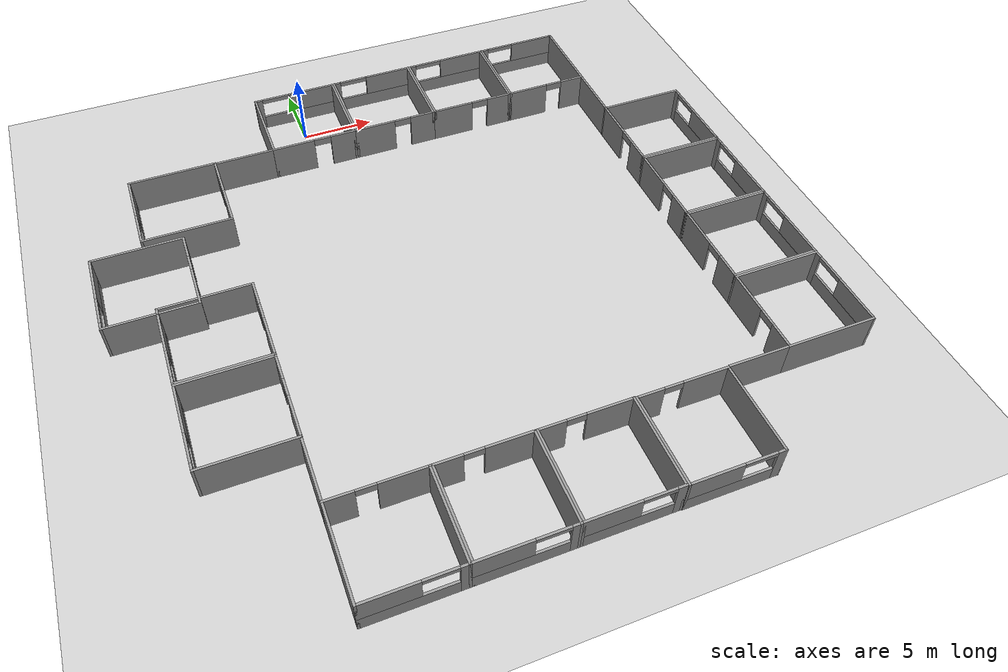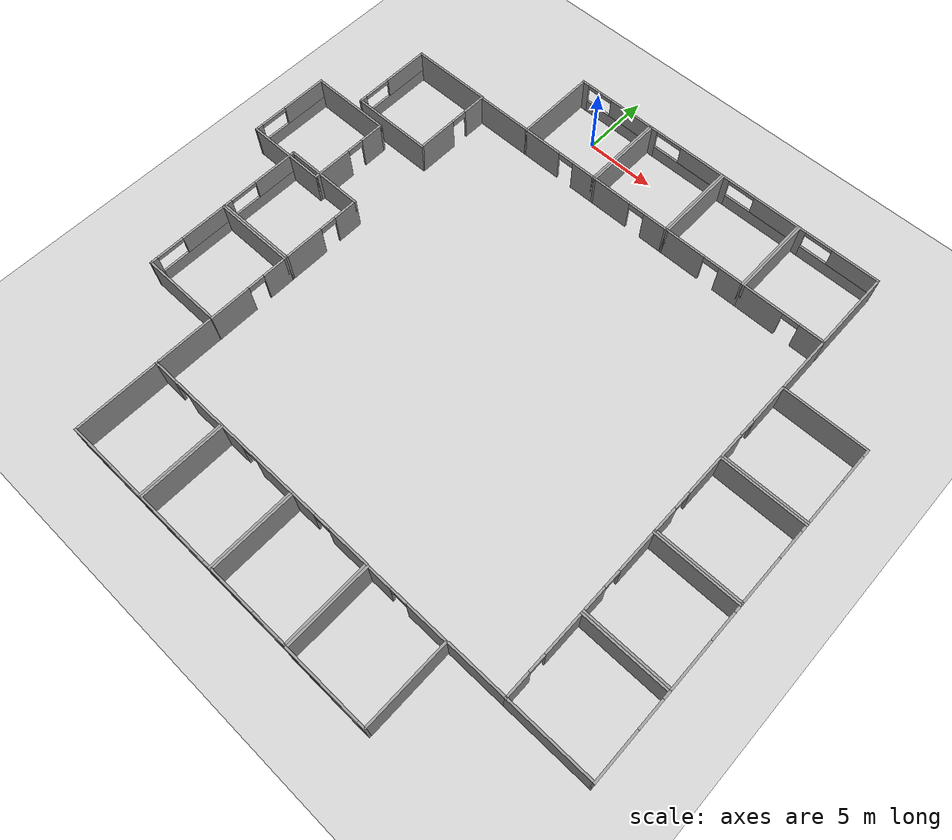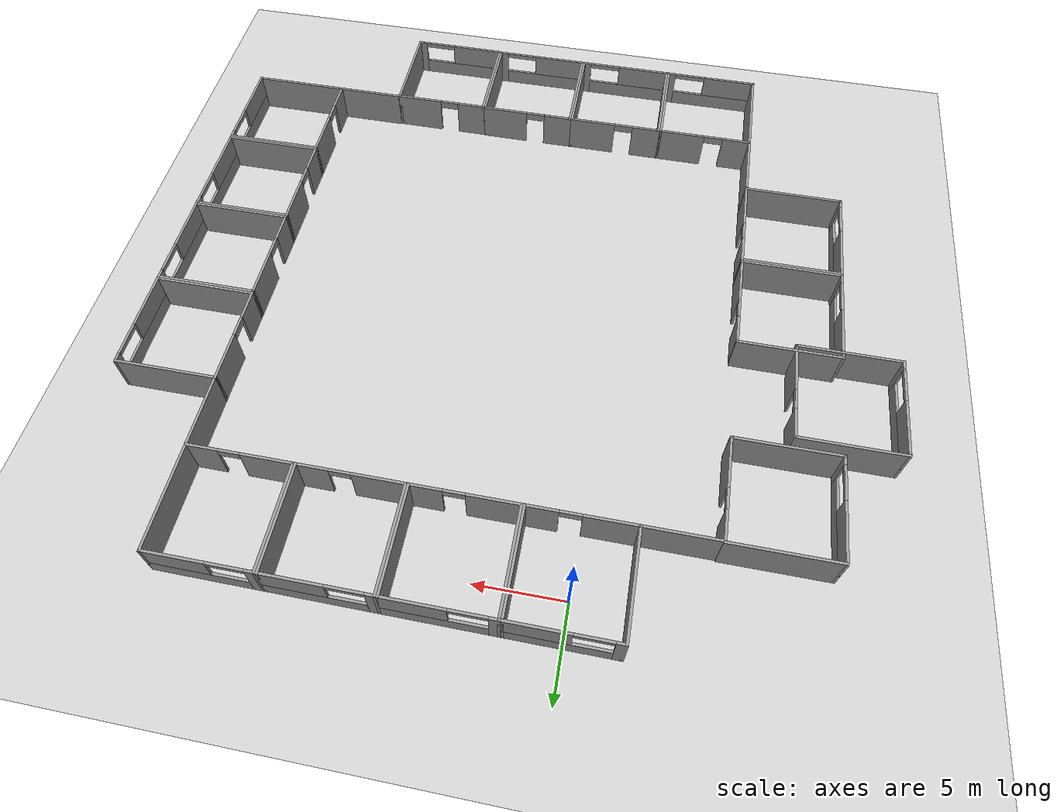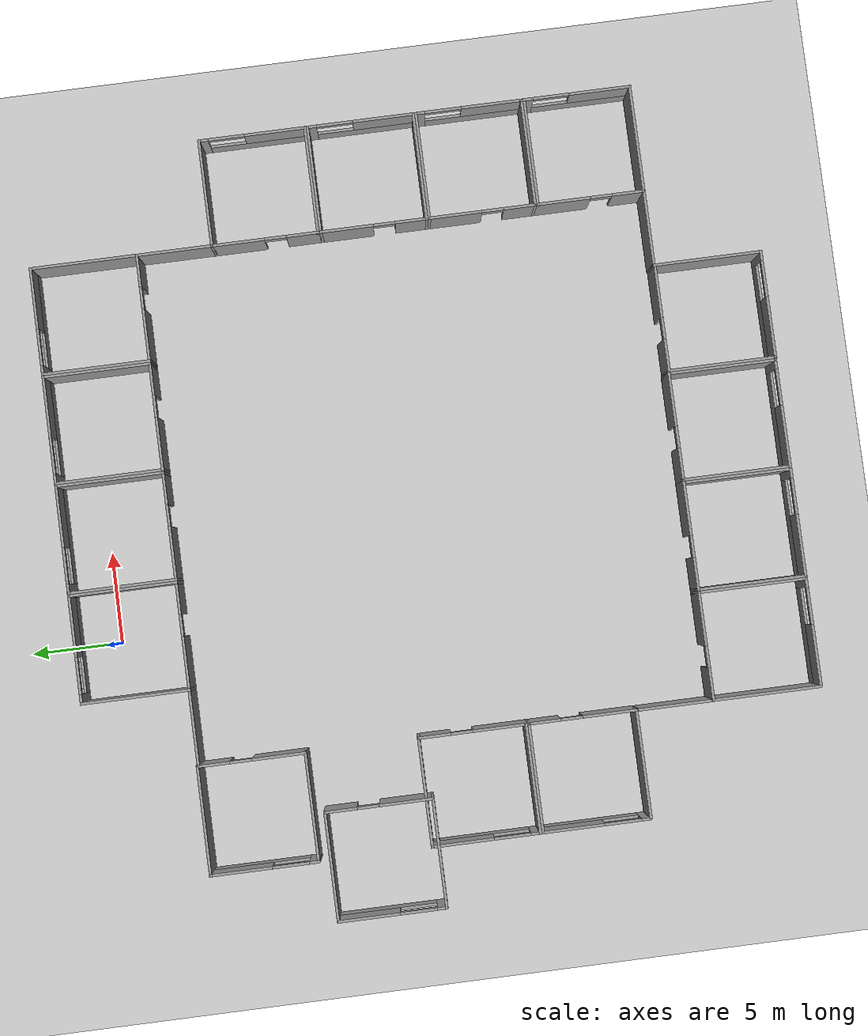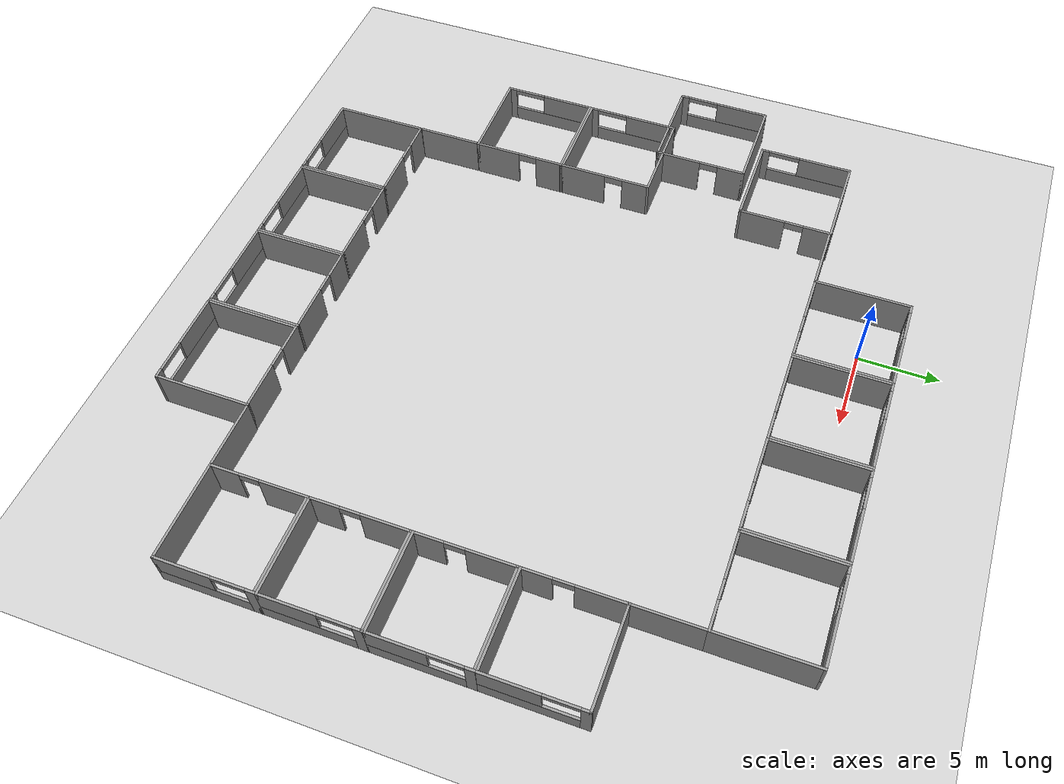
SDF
<sdf version="1.6">
 <world name="default">
  <light name="sun" type="directional">
   <pose>0 0 10 0 -0 0</pose>
   <diffuse>0.8 0.8 0.8 1</diffuse>
   <specular>0.2 0.2 0.2 1</specular>
   <attenuation>
    <range>1000</range>
    <constant>0.9</constant>
    <linear>0.01</linear>
    <quadratic>0.001</quadratic>
   </attenuation>
   <direction>-0.5 0.1 -0.9</direction>
  </light>
  <model name="ground_plane">
   <static>1</static>
   <link name="link">
    <collision name="collision">
     <geometry><plane><normal>0 0 1</normal><size>100 100</size></plane></geometry>
     <surface>
      <contact><collide_bitmask>65535</collide_bitmask></contact>
      <friction><ode><mu>100</mu><mu2>50</mu2></ode></friction>
     </surface>
    </collision>
    <visual name="visual">
     <cast_shadows>0</cast_shadows>
     <geometry><plane><normal>0 0 1</normal><size>100 100</size></plane></geometry>
     <material>
      <script><uri>file://media/materials/scripts/gazebo.material</uri><name>Gazebo/Grey</name></script>
     </material>
    </visual>
   </link>
  </model>
  <gravity>0 0 -9.8</gravity>
  <magnetic_field>6e-06 2.3e-05 -4.2e-05</magnetic_field>
  <atmosphere type="adiabatic"/>
  <physics name="default_physics" default="0" type="ode">
   <max_step_size>0.001</max_step_size>
   <real_time_factor>1</real_time_factor>
   <real_time_update_rate>1000</real_time_update_rate>
  </physics>
  <scene><ambient>0.4 0.4 0.4 1</ambient><background>0.7 0.7 0.7 1</background><shadows>1</shadows></scene>
  <spherical_coordinates>
   <surface_model>EARTH_WGS84</surface_model>
   <latitude_deg>0</latitude_deg>
   <longitude_deg>0</longitude_deg>
   <elevation>0</elevation>
   <heading_deg>0</heading_deg>
  </spherical_coordinates>
  <model name="patient_room">
   <link name="Wall_26">
    <pose>-0 2.218 0 0 -0 0</pose>
    <visual name="Wall_26_Visual_0">
     <pose>-2.7125 0 1.25 0 -0 0</pose>
     <geometry><box><size>0.575 0.15 2.5</size></box></geometry>
     <material>
      <script><uri>file://media/materials/scripts/gazebo.material</uri><name>Gazebo/Grey</name></script>
      <ambient>1 1 1 1</ambient>
     </material>
     <meta><layer>0</layer></meta>
    </visual>
    <collision name="Wall_26_Collision_0">
     <geometry><box><size>0.575 0.15 2.5</size></box></geometry>
     <pose>-2.7125 0 1.25 0 -0 0</pose>
    </collision>
    <visual name="Wall_26_Visual_1">
     <pose>0.2875 0 0.5 0 -0 0</pose>
     <geometry><box><size>5.425 0.15 1</size></box></geometry>
     <material>
      <script><uri>file://media/materials/scripts/gazebo.material</uri><name>Gazebo/Grey</name></script>
      <ambient>1 1 1 1</ambient>
     </material>
     <meta><layer>0</layer></meta>
    </visual>
    <collision name="Wall_26_Collision_1">
     <geometry><box><size>5.425 0.15 1</size></box></geometry>
     <pose>0.2875 0 0.5 0 -0 0</pose>
    </collision>
    <visual name="Wall_26_Visual_2">
     <pose>1.2875 0 1.75 0 -0 0</pose>
     <geometry><box><size>3.425 0.15 1.5</size></box></geometry>
     <material>
      <script><uri>file://media/materials/scripts/gazebo.material</uri><name>Gazebo/Grey</name></script>
      <ambient>1 1 1 1</ambient>
     </material>
     <meta><layer>0</layer></meta>
    </visual>
    <collision name="Wall_26_Collision_2">
     <geometry><box><size>3.425 0.15 1.5</size></box></geometry>
     <pose>1.2875 0 1.75 0 -0 0</pose>
    </collision>
    <visual name="Wall_26_Visual_3">
     <pose>-1.425 0 2.35 0 -0 0</pose>
     <geometry><box><size>2 0.15 0.3</size></box></geometry>
     <material>
      <script><uri>file://media/materials/scripts/gazebo.material</uri><name>Gazebo/Grey</name></script>
      <ambient>1 1 1 1</ambient>
     </material>
     <meta><layer>0</layer></meta>
    </visual>
    <collision name="Wall_26_Collision_3">
     <geometry><box><size>2 0.15 0.3</size></box></geometry>
     <pose>-1.425 0 2.35 0 -0 0</pose>
    </collision>
   </link>
   <link name="Wall_28">
    <collision name="Wall_28_Collision">
     <geometry><box><size>6 0.15 2.5</size></box></geometry>
     <pose>0 0 1.25 0 -0 0</pose>
    </collision>
    <visual name="Wall_28_Visual">
     <pose>0 0 1.25 0 -0 0</pose>
     <geometry><box><size>6 0.15 2.5</size></box></geometry>
     <material>
      <script><uri>file://media/materials/scripts/gazebo.material</uri><name>Gazebo/Grey</name></script>
      <ambient>1 1 1 1</ambient>
     </material>
     <meta><layer>0</layer></meta>
    </visual>
    <pose>-2.925 -0.707 0 0 -0 -1.5708</pose>
   </link>
   <link name="Wall_29">
    <pose>-0 -3.632 0 0 -0 0</pose>
    <visual name="Wall_29_Visual_0">
     <pose>-1.5125 0 1.25 0 -0 0</pose>
     <geometry><box><size>2.975 0.15 2.5</size></box></geometry>
     <material>
      <script><uri>file://media/materials/scripts/gazebo.material</uri><name>Gazebo/Grey</name></script>
      <ambient>1 1 1 1</ambient>
     </material>
     <meta><layer>0</layer></meta>
    </visual>
    <collision name="Wall_29_Collision_0">
     <geometry><box><size>2.975 0.15 2.5</size></box></geometry>
     <pose>-1.5125 0 1.25 0 -0 0</pose>
    </collision>
    <visual name="Wall_29_Visual_1">
     <pose>2.0875 0 1.25 0 -0 0</pose>
     <geometry><box><size>1.825 0.15 2.5</size></box></geometry>
     <material>
      <script><uri>file://media/materials/scripts/gazebo.material</uri><name>Gazebo/Grey</name></script>
      <ambient>1 1 1 1</ambient>
     </material>
     <meta><layer>0</layer></meta>
    </visual>
    <collision name="Wall_29_Collision_1">
     <geometry><box><size>1.825 0.15 2.5</size></box></geometry>
     <pose>2.0875 0 1.25 0 -0 0</pose>
    </collision>
    <visual name="Wall_29_Visual_2">
     <pose>0.575 0 2.25 0 -0 0</pose>
     <geometry><box><size>1.2 0.15 0.5</size></box></geometry>
     <material>
      <script><uri>file://media/materials/scripts/gazebo.material</uri><name>Gazebo/Grey</name></script>
      <ambient>1 1 1 1</ambient>
     </material>
     <meta><layer>0</layer></meta>
    </visual>
    <collision name="Wall_29_Collision_2">
     <geometry><box><size>1.2 0.15 0.5</size></box></geometry>
     <pose>0.575 0 2.25 0 -0 0</pose>
    </collision>
   </link>
   <link name="Wall_30">
    <collision name="Wall_30_Collision">
     <geometry><box><size>6 0.15 2.5</size></box></geometry>
     <pose>0 0 1.25 0 -0 0</pose>
    </collision>
    <visual name="Wall_30_Visual">
     <pose>0 0 1.25 0 -0 0</pose>
     <geometry><box><size>6 0.15 2.5</size></box></geometry>
     <material>
      <script><uri>file://media/materials/scripts/gazebo.material</uri><name>Gazebo/Grey</name></script>
      <ambient>1 1 1 1</ambient>
     </material>
     <meta><layer>0</layer></meta>
    </visual>
    <pose>2.925 -0.707 0 0 -0 1.5708</pose>
   </link>
   <static>1</static>
  </model>
  <model name="patient_room_clone">
   <pose>6 0 0 0 -0 0</pose>
   <link name="Wall_26">
    <pose>-0 2.218 0 0 -0 0</pose>
    <visual name="Wall_26_Visual_0">
     <pose>-2.7125 0 1.25 0 -0 0</pose>
     <geometry><box><size>0.575 0.15 2.5</size></box></geometry>
     <material>
      <script><uri>file://media/materials/scripts/gazebo.material</uri><name>Gazebo/Grey</name></script>
      <ambient>1 1 1 1</ambient>
     </material>
     <meta><layer>0</layer></meta>
    </visual>
    <collision name="Wall_26_Collision_0">
     <geometry><box><size>0.575 0.15 2.5</size></box></geometry>
     <pose>-2.7125 0 1.25 0 -0 0</pose>
    </collision>
    <visual name="Wall_26_Visual_1">
     <pose>0.2875 0 0.5 0 -0 0</pose>
     <geometry><box><size>5.425 0.15 1</size></box></geometry>
     <material>
      <script><uri>file://media/materials/scripts/gazebo.material</uri><name>Gazebo/Grey</name></script>
      <ambient>1 1 1 1</ambient>
     </material>
     <meta><layer>0</layer></meta>
    </visual>
    <collision name="Wall_26_Collision_1">
     <geometry><box><size>5.425 0.15 1</size></box></geometry>
     <pose>0.2875 0 0.5 0 -0 0</pose>
    </collision>
    <visual name="Wall_26_Visual_2">
     <pose>1.2875 0 1.75 0 -0 0</pose>
     <geometry><box><size>3.425 0.15 1.5</size></box></geometry>
     <material>
      <script><uri>file://media/materials/scripts/gazebo.material</uri><name>Gazebo/Grey</name></script>
      <ambient>1 1 1 1</ambient>
     </material>
     <meta><layer>0</layer></meta>
    </visual>
    <collision name="Wall_26_Collision_2">
     <geometry><box><size>3.425 0.15 1.5</size></box></geometry>
     <pose>1.2875 0 1.75 0 -0 0</pose>
    </collision>
    <visual name="Wall_26_Visual_3">
     <pose>-1.425 0 2.35 0 -0 0</pose>
     <geometry><box><size>2 0.15 0.3</size></box></geometry>
     <material>
      <script><uri>file://media/materials/scripts/gazebo.material</uri><name>Gazebo/Grey</name></script>
      <ambient>1 1 1 1</ambient>
     </material>
     <meta><layer>0</layer></meta>
    </visual>
    <collision name="Wall_26_Collision_3">
     <geometry><box><size>2 0.15 0.3</size></box></geometry>
     <pose>-1.425 0 2.35 0 -0 0</pose>
    </collision>
   </link>
   <link name="Wall_28">
    <collision name="Wall_28_Collision">
     <geometry><box><size>6 0.15 2.5</size></box></geometry>
     <pose>0 0 1.25 0 -0 0</pose>
    </collision>
    <visual name="Wall_28_Visual">
     <pose>0 0 1.25 0 -0 0</pose>
     <geometry><box><size>6 0.15 2.5</size></box></geometry>
     <material>
      <script><uri>file://media/materials/scripts/gazebo.material</uri><name>Gazebo/Grey</name></script>
      <ambient>1 1 1 1</ambient>
     </material>
     <meta><layer>0</layer></meta>
    </visual>
    <pose>-2.925 -0.707 0 0 -0 -1.5708</pose>
   </link>
   <link name="Wall_29">
    <pose>-0 -3.632 0 0 -0 0</pose>
    <visual name="Wall_29_Visual_0">
     <pose>-1.5125 0 1.25 0 -0 0</pose>
     <geometry><box><size>2.975 0.15 2.5</size></box></geometry>
     <material>
      <script><uri>file://media/materials/scripts/gazebo.material</uri><name>Gazebo/Grey</name></script>
      <ambient>1 1 1 1</ambient>
     </material>
     <meta><layer>0</layer></meta>
    </visual>
    <collision name="Wall_29_Collision_0">
     <geometry><box><size>2.975 0.15 2.5</size></box></geometry>
     <pose>-1.5125 0 1.25 0 -0 0</pose>
    </collision>
    <visual name="Wall_29_Visual_1">
     <pose>2.0875 0 1.25 0 -0 0</pose>
     <geometry><box><size>1.825 0.15 2.5</size></box></geometry>
     <material>
      <script><uri>file://media/materials/scripts/gazebo.material</uri><name>Gazebo/Grey</name></script>
      <ambient>1 1 1 1</ambient>
     </material>
     <meta><layer>0</layer></meta>
    </visual>
    <collision name="Wall_29_Collision_1">
     <geometry><box><size>1.825 0.15 2.5</size></box></geometry>
     <pose>2.0875 0 1.25 0 -0 0</pose>
    </collision>
    <visual name="Wall_29_Visual_2">
     <pose>0.575 0 2.25 0 -0 0</pose>
     <geometry><box><size>1.2 0.15 0.5</size></box></geometry>
     <material>
      <script><uri>file://media/materials/scripts/gazebo.material</uri><name>Gazebo/Grey</name></script>
      <ambient>1 1 1 1</ambient>
     </material>
     <meta><layer>0</layer></meta>
    </visual>
    <collision name="Wall_29_Collision_2">
     <geometry><box><size>1.2 0.15 0.5</size></box></geometry>
     <pose>0.575 0 2.25 0 -0 0</pose>
    </collision>
   </link>
   <link name="Wall_30">
    <collision name="Wall_30_Collision">
     <geometry><box><size>6 0.15 2.5</size></box></geometry>
     <pose>0 0 1.25 0 -0 0</pose>
    </collision>
    <visual name="Wall_30_Visual">
     <pose>0 0 1.25 0 -0 0</pose>
     <geometry><box><size>6 0.15 2.5</size></box></geometry>
     <material>
      <script><uri>file://media/materials/scripts/gazebo.material</uri><name>Gazebo/Grey</name></script>
      <ambient>1 1 1 1</ambient>
     </material>
     <meta><layer>0</layer></meta>
    </visual>
    <pose>2.925 -0.707 0 0 -0 1.5708</pose>
   </link>
   <static>1</static>
  </model>
  <model name="patient_room_clone_1">
   <pose>12 0 0 0 -0 0</pose>
   <link name="Wall_26">
    <pose>-0 2.218 0 0 -0 0</pose>
    <visual name="Wall_26_Visual_0">
     <pose>-2.7125 0 1.25 0 -0 0</pose>
     <geometry><box><size>0.575 0.15 2.5</size></box></geometry>
     <material>
      <script><uri>file://media/materials/scripts/gazebo.material</uri><name>Gazebo/Grey</name></script>
      <ambient>1 1 1 1</ambient>
     </material>
     <meta><layer>0</layer></meta>
    </visual>
    <collision name="Wall_26_Collision_0">
     <geometry><box><size>0.575 0.15 2.5</size></box></geometry>
     <pose>-2.7125 0 1.25 0 -0 0</pose>
    </collision>
    <visual name="Wall_26_Visual_1">
     <pose>0.2875 0 0.5 0 -0 0</pose>
     <geometry><box><size>5.425 0.15 1</size></box></geometry>
     <material>
      <script><uri>file://media/materials/scripts/gazebo.material</uri><name>Gazebo/Grey</name></script>
      <ambient>1 1 1 1</ambient>
     </material>
     <meta><layer>0</layer></meta>
    </visual>
    <collision name="Wall_26_Collision_1">
     <geometry><box><size>5.425 0.15 1</size></box></geometry>
     <pose>0.2875 0 0.5 0 -0 0</pose>
    </collision>
    <visual name="Wall_26_Visual_2">
     <pose>1.2875 0 1.75 0 -0 0</pose>
     <geometry><box><size>3.425 0.15 1.5</size></box></geometry>
     <material>
      <script><uri>file://media/materials/scripts/gazebo.material</uri><name>Gazebo/Grey</name></script>
      <ambient>1 1 1 1</ambient>
     </material>
     <meta><layer>0</layer></meta>
    </visual>
    <collision name="Wall_26_Collision_2">
     <geometry><box><size>3.425 0.15 1.5</size></box></geometry>
     <pose>1.2875 0 1.75 0 -0 0</pose>
    </collision>
    <visual name="Wall_26_Visual_3">
     <pose>-1.425 0 2.35 0 -0 0</pose>
     <geometry><box><size>2 0.15 0.3</size></box></geometry>
     <material>
      <script><uri>file://media/materials/scripts/gazebo.material</uri><name>Gazebo/Grey</name></script>
      <ambient>1 1 1 1</ambient>
     </material>
     <meta><layer>0</layer></meta>
    </visual>
    <collision name="Wall_26_Collision_3">
     <geometry><box><size>2 0.15 0.3</size></box></geometry>
     <pose>-1.425 0 2.35 0 -0 0</pose>
    </collision>
   </link>
   <link name="Wall_28">
    <collision name="Wall_28_Collision">
     <geometry><box><size>6 0.15 2.5</size></box></geometry>
     <pose>0 0 1.25 0 -0 0</pose>
    </collision>
    <visual name="Wall_28_Visual">
     <pose>0 0 1.25 0 -0 0</pose>
     <geometry><box><size>6 0.15 2.5</size></box></geometry>
     <material>
      <script><uri>file://media/materials/scripts/gazebo.material</uri><name>Gazebo/Grey</name></script>
      <ambient>1 1 1 1</ambient>
     </material>
     <meta><layer>0</layer></meta>
    </visual>
    <pose>-2.925 -0.707 0 0 -0 -1.5708</pose>
   </link>
   <link name="Wall_29">
    <pose>-0 -3.632 0 0 -0 0</pose>
    <visual name="Wall_29_Visual_0">
     <pose>-1.5125 0 1.25 0 -0 0</pose>
     <geometry><box><size>2.975 0.15 2.5</size></box></geometry>
     <material>
      <script><uri>file://media/materials/scripts/gazebo.material</uri><name>Gazebo/Grey</name></script>
      <ambient>1 1 1 1</ambient>
     </material>
     <meta><layer>0</layer></meta>
    </visual>
    <collision name="Wall_29_Collision_0">
     <geometry><box><size>2.975 0.15 2.5</size></box></geometry>
     <pose>-1.5125 0 1.25 0 -0 0</pose>
    </collision>
    <visual name="Wall_29_Visual_1">
     <pose>2.0875 0 1.25 0 -0 0</pose>
     <geometry><box><size>1.825 0.15 2.5</size></box></geometry>
     <material>
      <script><uri>file://media/materials/scripts/gazebo.material</uri><name>Gazebo/Grey</name></script>
      <ambient>1 1 1 1</ambient>
     </material>
     <meta><layer>0</layer></meta>
    </visual>
    <collision name="Wall_29_Collision_1">
     <geometry><box><size>1.825 0.15 2.5</size></box></geometry>
     <pose>2.0875 0 1.25 0 -0 0</pose>
    </collision>
    <visual name="Wall_29_Visual_2">
     <pose>0.575 0 2.25 0 -0 0</pose>
     <geometry><box><size>1.2 0.15 0.5</size></box></geometry>
     <material>
      <script><uri>file://media/materials/scripts/gazebo.material</uri><name>Gazebo/Grey</name></script>
      <ambient>1 1 1 1</ambient>
     </material>
     <meta><layer>0</layer></meta>
    </visual>
    <collision name="Wall_29_Collision_2">
     <geometry><box><size>1.2 0.15 0.5</size></box></geometry>
     <pose>0.575 0 2.25 0 -0 0</pose>
    </collision>
   </link>
   <link name="Wall_30">
    <collision name="Wall_30_Collision">
     <geometry><box><size>6 0.15 2.5</size></box></geometry>
     <pose>0 0 1.25 0 -0 0</pose>
    </collision>
    <visual name="Wall_30_Visual">
     <pose>0 0 1.25 0 -0 0</pose>
     <geometry><box><size>6 0.15 2.5</size></box></geometry>
     <material>
      <script><uri>file://media/materials/scripts/gazebo.material</uri><name>Gazebo/Grey</name></script>
      <ambient>1 1 1 1</ambient>
     </material>
     <meta><layer>0</layer></meta>
    </visual>
    <pose>2.925 -0.707 0 0 -0 1.5708</pose>
   </link>
   <static>1</static>
  </model>
  <model name="patient_room_clone_3">
   <pose>18 0 0 0 -0 0</pose>
   <link name="Wall_26">
    <pose>-0 2.218 0 0 -0 0</pose>
    <visual name="Wall_26_Visual_0">
     <pose>-2.7125 0 1.25 0 -0 0</pose>
     <geometry><box><size>0.575 0.15 2.5</size></box></geometry>
     <material>
      <script><uri>file://media/materials/scripts/gazebo.material</uri><name>Gazebo/Grey</name></script>
      <ambient>1 1 1 1</ambient>
     </material>
     <meta><layer>0</layer></meta>
    </visual>
    <collision name="Wall_26_Collision_0">
     <geometry><box><size>0.575 0.15 2.5</size></box></geometry>
     <pose>-2.7125 0 1.25 0 -0 0</pose>
    </collision>
    <visual name="Wall_26_Visual_1">
     <pose>0.2875 0 0.5 0 -0 0</pose>
     <geometry><box><size>5.425 0.15 1</size></box></geometry>
     <material>
      <script><uri>file://media/materials/scripts/gazebo.material</uri><name>Gazebo/Grey</name></script>
      <ambient>1 1 1 1</ambient>
     </material>
     <meta><layer>0</layer></meta>
    </visual>
    <collision name="Wall_26_Collision_1">
     <geometry><box><size>5.425 0.15 1</size></box></geometry>
     <pose>0.2875 0 0.5 0 -0 0</pose>
    </collision>
    <visual name="Wall_26_Visual_2">
     <pose>1.2875 0 1.75 0 -0 0</pose>
     <geometry><box><size>3.425 0.15 1.5</size></box></geometry>
     <material>
      <script><uri>file://media/materials/scripts/gazebo.material</uri><name>Gazebo/Grey</name></script>
      <ambient>1 1 1 1</ambient>
     </material>
     <meta><layer>0</layer></meta>
    </visual>
    <collision name="Wall_26_Collision_2">
     <geometry><box><size>3.425 0.15 1.5</size></box></geometry>
     <pose>1.2875 0 1.75 0 -0 0</pose>
    </collision>
    <visual name="Wall_26_Visual_3">
     <pose>-1.425 0 2.35 0 -0 0</pose>
     <geometry><box><size>2 0.15 0.3</size></box></geometry>
     <material>
      <script><uri>file://media/materials/scripts/gazebo.material</uri><name>Gazebo/Grey</name></script>
      <ambient>1 1 1 1</ambient>
     </material>
     <meta><layer>0</layer></meta>
    </visual>
    <collision name="Wall_26_Collision_3">
     <geometry><box><size>2 0.15 0.3</size></box></geometry>
     <pose>-1.425 0 2.35 0 -0 0</pose>
    </collision>
   </link>
   <link name="Wall_28">
    <collision name="Wall_28_Collision">
     <geometry><box><size>6 0.15 2.5</size></box></geometry>
     <pose>0 0 1.25 0 -0 0</pose>
    </collision>
    <visual name="Wall_28_Visual">
     <pose>0 0 1.25 0 -0 0</pose>
     <geometry><box><size>6 0.15 2.5</size></box></geometry>
     <material>
      <script><uri>file://media/materials/scripts/gazebo.material</uri><name>Gazebo/Grey</name></script>
      <ambient>1 1 1 1</ambient>
     </material>
     <meta><layer>0</layer></meta>
    </visual>
    <pose>-2.925 -0.707 0 0 -0 -1.5708</pose>
   </link>
   <link name="Wall_29">
    <pose>-0 -3.632 0 0 -0 0</pose>
    <visual name="Wall_29_Visual_0">
     <pose>-1.5125 0 1.25 0 -0 0</pose>
     <geometry><box><size>2.975 0.15 2.5</size></box></geometry>
     <material>
      <script><uri>file://media/materials/scripts/gazebo.material</uri><name>Gazebo/Grey</name></script>
      <ambient>1 1 1 1</ambient>
     </material>
     <meta><layer>0</layer></meta>
    </visual>
    <collision name="Wall_29_Collision_0">
     <geometry><box><size>2.975 0.15 2.5</size></box></geometry>
     <pose>-1.5125 0 1.25 0 -0 0</pose>
    </collision>
    <visual name="Wall_29_Visual_1">
     <pose>2.0875 0 1.25 0 -0 0</pose>
     <geometry><box><size>1.825 0.15 2.5</size></box></geometry>
     <material>
      <script><uri>file://media/materials/scripts/gazebo.material</uri><name>Gazebo/Grey</name></script>
      <ambient>1 1 1 1</ambient>
     </material>
     <meta><layer>0</layer></meta>
    </visual>
    <collision name="Wall_29_Collision_1">
     <geometry><box><size>1.825 0.15 2.5</size></box></geometry>
     <pose>2.0875 0 1.25 0 -0 0</pose>
    </collision>
    <visual name="Wall_29_Visual_2">
     <pose>0.575 0 2.25 0 -0 0</pose>
     <geometry><box><size>1.2 0.15 0.5</size></box></geometry>
     <material>
      <script><uri>file://media/materials/scripts/gazebo.material</uri><name>Gazebo/Grey</name></script>
      <ambient>1 1 1 1</ambient>
     </material>
     <meta><layer>0</layer></meta>
    </visual>
    <collision name="Wall_29_Collision_2">
     <geometry><box><size>1.2 0.15 0.5</size></box></geometry>
     <pose>0.575 0 2.25 0 -0 0</pose>
    </collision>
   </link>
   <link name="Wall_30">
    <collision name="Wall_30_Collision">
     <geometry><box><size>6 0.15 2.5</size></box></geometry>
     <pose>0 0 1.25 0 -0 0</pose>
    </collision>
    <visual name="Wall_30_Visual">
     <pose>0 0 1.25 0 -0 0</pose>
     <geometry><box><size>6 0.15 2.5</size></box></geometry>
     <material>
      <script><uri>file://media/materials/scripts/gazebo.material</uri><name>Gazebo/Grey</name></script>
      <ambient>1 1 1 1</ambient>
     </material>
     <meta><layer>0</layer></meta>
    </visual>
    <pose>2.925 -0.707 0 0 -0 1.5708</pose>
   </link>
   <static>1</static>
  </model>
  <model name="wall_4m">
   <pose>-5.76 2.84 0 0 -0 0</pose>
   <link name="Wall_36">
    <collision name="Wall_36_Collision">
     <geometry><box><size>4 0.15 2.5</size></box></geometry>
     <pose>0 0 1.25 0 -0 0</pose>
    </collision>
    <visual name="Wall_36_Visual">
     <pose>0 0 1.25 0 -0 0</pose>
     <geometry><box><size>4 0.15 2.5</size></box></geometry>
     <material>
      <script><uri>file://media/materials/scripts/gazebo.material</uri><name>Gazebo/Grey</name></script>
      <ambient>1 1 1 1</ambient>
     </material>
     <meta><layer>0</layer></meta>
    </visual>
    <pose>0.760563 -6.47163 0 0 -0 0</pose>
   </link>
   <static>1</static>
  </model>
  <model name="wall_4m_0">
   <pose>-13.55 -30.2927 0 0 -0 1.5708</pose>
   <link name="Wall_36">
    <collision name="Wall_36_Collision">
     <geometry><box><size>4 0.15 2.5</size></box></geometry>
     <pose>0 0 1.25 0 -0 0</pose>
    </collision>
    <visual name="Wall_36_Visual">
     <pose>0 0 1.25 0 -0 0</pose>
     <geometry><box><size>4 0.15 2.5</size></box></geometry>
     <material>
      <script><uri>file://media/materials/scripts/gazebo.material</uri><name>Gazebo/Grey</name></script>
      <ambient>1 1 1 1</ambient>
     </material>
     <meta><layer>0</layer></meta>
    </visual>
    <pose>0.760563 -6.47163 0 0 -0 0</pose>
   </link>
   <static>1</static>
  </model>
  <model name="wall_4m_1">
   <pose>14.4505 -6.46035 0 0 -0 1.5708</pose>
   <link name="Wall_36">
    <collision name="Wall_36_Collision">
     <geometry><box><size>4 0.15 2.5</size></box></geometry>
     <pose>0 0 1.25 0 -0 0</pose>
    </collision>
    <visual name="Wall_36_Visual">
     <pose>0 0 1.25 0 -0 0</pose>
     <geometry><box><size>4 0.15 2.5</size></box></geometry>
     <material>
      <script><uri>file://media/materials/scripts/gazebo.material</uri><name>Gazebo/Grey</name></script>
      <ambient>1 1 1 1</ambient>
     </material>
     <meta><layer>0</layer></meta>
    </visual>
    <pose>0.760563 -6.47163 0 0 -0 0</pose>
   </link>
   <static>1</static>
  </model>
  <model name="wall_4m_2">
   <pose>18.0836 -25.1539 0 0 -0 0</pose>
   <link name="Wall_36">
    <collision name="Wall_36_Collision">
     <geometry><box><size>4 0.15 2.5</size></box></geometry>
     <pose>0 0 1.25 0 -0 0</pose>
    </collision>
    <visual name="Wall_36_Visual">
     <pose>0 0 1.25 0 -0 0</pose>
     <geometry><box><size>4 0.15 2.5</size></box></geometry>
     <material>
      <script><uri>file://media/materials/scripts/gazebo.material</uri><name>Gazebo/Grey</name></script>
      <ambient>1 1 1 1</ambient>
     </material>
     <meta><layer>0</layer></meta>
    </visual>
    <pose>0.760563 -6.47163 0 0 -0 0</pose>
   </link>
   <static>1</static>
  </model>
  <model name="patient_room_clone_3_clone">
   <pose>7.85 -35.26 0 0 -0 -3.14159</pose>
   <link name="Wall_26">
    <pose>-0 2.218 0 0 -0 0</pose>
    <visual name="Wall_26_Visual_0">
     <pose>-2.7125 0 1.25 0 -0 0</pose>
     <geometry><box><size>0.575 0.15 2.5</size></box></geometry>
     <material>
      <script><uri>file://media/materials/scripts/gazebo.material</uri><name>Gazebo/Grey</name></script>
      <ambient>1 1 1 1</ambient>
     </material>
     <meta><layer>0</layer></meta>
    </visual>
    <collision name="Wall_26_Collision_0">
     <geometry><box><size>0.575 0.15 2.5</size></box></geometry>
     <pose>-2.7125 0 1.25 0 -0 0</pose>
    </collision>
    <visual name="Wall_26_Visual_1">
     <pose>0.2875 0 0.5 0 -0 0</pose>
     <geometry><box><size>5.425 0.15 1</size></box></geometry>
     <material>
      <script><uri>file://media/materials/scripts/gazebo.material</uri><name>Gazebo/Grey</name></script>
      <ambient>1 1 1 1</ambient>
     </material>
     <meta><layer>0</layer></meta>
    </visual>
    <collision name="Wall_26_Collision_1">
     <geometry><box><size>5.425 0.15 1</size></box></geometry>
     <pose>0.2875 0 0.5 0 -0 0</pose>
    </collision>
    <visual name="Wall_26_Visual_2">
     <pose>1.2875 0 1.75 0 -0 0</pose>
     <geometry><box><size>3.425 0.15 1.5</size></box></geometry>
     <material>
      <script><uri>file://media/materials/scripts/gazebo.material</uri><name>Gazebo/Grey</name></script>
      <ambient>1 1 1 1</ambient>
     </material>
     <meta><layer>0</layer></meta>
    </visual>
    <collision name="Wall_26_Collision_2">
     <geometry><box><size>3.425 0.15 1.5</size></box></geometry>
     <pose>1.2875 0 1.75 0 -0 0</pose>
    </collision>
    <visual name="Wall_26_Visual_3">
     <pose>-1.425 0 2.35 0 -0 0</pose>
     <geometry><box><size>2 0.15 0.3</size></box></geometry>
     <material>
      <script><uri>file://media/materials/scripts/gazebo.material</uri><name>Gazebo/Grey</name></script>
      <ambient>1 1 1 1</ambient>
     </material>
     <meta><layer>0</layer></meta>
    </visual>
    <collision name="Wall_26_Collision_3">
     <geometry><box><size>2 0.15 0.3</size></box></geometry>
     <pose>-1.425 0 2.35 0 -0 0</pose>
    </collision>
   </link>
   <link name="Wall_28">
    <collision name="Wall_28_Collision">
     <geometry><box><size>6 0.15 2.5</size></box></geometry>
     <pose>0 0 1.25 0 -0 0</pose>
    </collision>
    <visual name="Wall_28_Visual">
     <pose>0 0 1.25 0 -0 0</pose>
     <geometry><box><size>6 0.15 2.5</size></box></geometry>
     <material>
      <script><uri>file://media/materials/scripts/gazebo.material</uri><name>Gazebo/Grey</name></script>
      <ambient>1 1 1 1</ambient>
     </material>
     <meta><layer>0</layer></meta>
    </visual>
    <pose>-2.925 -0.707 0 0 -0 -1.5708</pose>
   </link>
   <link name="Wall_29">
    <pose>-0 -3.632 0 0 -0 0</pose>
    <visual name="Wall_29_Visual_0">
     <pose>-1.5125 0 1.25 0 -0 0</pose>
     <geometry><box><size>2.975 0.15 2.5</size></box></geometry>
     <material>
      <script><uri>file://media/materials/scripts/gazebo.material</uri><name>Gazebo/Grey</name></script>
      <ambient>1 1 1 1</ambient>
     </material>
     <meta><layer>0</layer></meta>
    </visual>
    <collision name="Wall_29_Collision_0">
     <geometry><box><size>2.975 0.15 2.5</size></box></geometry>
     <pose>-1.5125 0 1.25 0 -0 0</pose>
    </collision>
    <visual name="Wall_29_Visual_1">
     <pose>2.0875 0 1.25 0 -0 0</pose>
     <geometry><box><size>1.825 0.15 2.5</size></box></geometry>
     <material>
      <script><uri>file://media/materials/scripts/gazebo.material</uri><name>Gazebo/Grey</name></script>
      <ambient>1 1 1 1</ambient>
     </material>
     <meta><layer>0</layer></meta>
    </visual>
    <collision name="Wall_29_Collision_1">
     <geometry><box><size>1.825 0.15 2.5</size></box></geometry>
     <pose>2.0875 0 1.25 0 -0 0</pose>
    </collision>
    <visual name="Wall_29_Visual_2">
     <pose>0.575 0 2.25 0 -0 0</pose>
     <geometry><box><size>1.2 0.15 0.5</size></box></geometry>
     <material>
      <script><uri>file://media/materials/scripts/gazebo.material</uri><name>Gazebo/Grey</name></script>
      <ambient>1 1 1 1</ambient>
     </material>
     <meta><layer>0</layer></meta>
    </visual>
    <collision name="Wall_29_Collision_2">
     <geometry><box><size>1.2 0.15 0.5</size></box></geometry>
     <pose>0.575 0 2.25 0 -0 0</pose>
    </collision>
   </link>
   <link name="Wall_30">
    <collision name="Wall_30_Collision">
     <geometry><box><size>6 0.15 2.5</size></box></geometry>
     <pose>0 0 1.25 0 -0 0</pose>
    </collision>
    <visual name="Wall_30_Visual">
     <pose>0 0 1.25 0 -0 0</pose>
     <geometry><box><size>6 0.15 2.5</size></box></geometry>
     <material>
      <script><uri>file://media/materials/scripts/gazebo.material</uri><name>Gazebo/Grey</name></script>
      <ambient>1 1 1 1</ambient>
     </material>
     <meta><layer>0</layer></meta>
    </visual>
    <pose>2.925 -0.707 0 0 -0 1.5708</pose>
   </link>
   <static>1</static>
  </model>
  <model name="patient_room_clone_3_clone_clone">
   <pose>1.85 -35.26 0 0 -0 3.14159</pose>
   <link name="Wall_26">
    <pose>-0 2.218 0 0 -0 0</pose>
    <visual name="Wall_26_Visual_0">
     <pose>-2.7125 0 1.25 0 -0 0</pose>
     <geometry><box><size>0.575 0.15 2.5</size></box></geometry>
     <material>
      <script><uri>file://media/materials/scripts/gazebo.material</uri><name>Gazebo/Grey</name></script>
      <ambient>1 1 1 1</ambient>
     </material>
     <meta><layer>0</layer></meta>
    </visual>
    <collision name="Wall_26_Collision_0">
     <geometry><box><size>0.575 0.15 2.5</size></box></geometry>
     <pose>-2.7125 0 1.25 0 -0 0</pose>
    </collision>
    <visual name="Wall_26_Visual_1">
     <pose>0.2875 0 0.5 0 -0 0</pose>
     <geometry><box><size>5.425 0.15 1</size></box></geometry>
     <material>
      <script><uri>file://media/materials/scripts/gazebo.material</uri><name>Gazebo/Grey</name></script>
      <ambient>1 1 1 1</ambient>
     </material>
     <meta><layer>0</layer></meta>
    </visual>
    <collision name="Wall_26_Collision_1">
     <geometry><box><size>5.425 0.15 1</size></box></geometry>
     <pose>0.2875 0 0.5 0 -0 0</pose>
    </collision>
    <visual name="Wall_26_Visual_2">
     <pose>1.2875 0 1.75 0 -0 0</pose>
     <geometry><box><size>3.425 0.15 1.5</size></box></geometry>
     <material>
      <script><uri>file://media/materials/scripts/gazebo.material</uri><name>Gazebo/Grey</name></script>
      <ambient>1 1 1 1</ambient>
     </material>
     <meta><layer>0</layer></meta>
    </visual>
    <collision name="Wall_26_Collision_2">
     <geometry><box><size>3.425 0.15 1.5</size></box></geometry>
     <pose>1.2875 0 1.75 0 -0 0</pose>
    </collision>
    <visual name="Wall_26_Visual_3">
     <pose>-1.425 0 2.35 0 -0 0</pose>
     <geometry><box><size>2 0.15 0.3</size></box></geometry>
     <material>
      <script><uri>file://media/materials/scripts/gazebo.material</uri><name>Gazebo/Grey</name></script>
      <ambient>1 1 1 1</ambient>
     </material>
     <meta><layer>0</layer></meta>
    </visual>
    <collision name="Wall_26_Collision_3">
     <geometry><box><size>2 0.15 0.3</size></box></geometry>
     <pose>-1.425 0 2.35 0 -0 0</pose>
    </collision>
   </link>
   <link name="Wall_28">
    <collision name="Wall_28_Collision">
     <geometry><box><size>6 0.15 2.5</size></box></geometry>
     <pose>0 0 1.25 0 -0 0</pose>
    </collision>
    <visual name="Wall_28_Visual">
     <pose>0 0 1.25 0 -0 0</pose>
     <geometry><box><size>6 0.15 2.5</size></box></geometry>
     <material>
      <script><uri>file://media/materials/scripts/gazebo.material</uri><name>Gazebo/Grey</name></script>
      <ambient>1 1 1 1</ambient>
     </material>
     <meta><layer>0</layer></meta>
    </visual>
    <pose>-2.925 -0.707 0 0 -0 -1.5708</pose>
   </link>
   <link name="Wall_29">
    <pose>-0 -3.632 0 0 -0 0</pose>
    <visual name="Wall_29_Visual_0">
     <pose>-1.5125 0 1.25 0 -0 0</pose>
     <geometry><box><size>2.975 0.15 2.5</size></box></geometry>
     <material>
      <script><uri>file://media/materials/scripts/gazebo.material</uri><name>Gazebo/Grey</name></script>
      <ambient>1 1 1 1</ambient>
     </material>
     <meta><layer>0</layer></meta>
    </visual>
    <collision name="Wall_29_Collision_0">
     <geometry><box><size>2.975 0.15 2.5</size></box></geometry>
     <pose>-1.5125 0 1.25 0 -0 0</pose>
    </collision>
    <visual name="Wall_29_Visual_1">
     <pose>2.0875 0 1.25 0 -0 0</pose>
     <geometry><box><size>1.825 0.15 2.5</size></box></geometry>
     <material>
      <script><uri>file://media/materials/scripts/gazebo.material</uri><name>Gazebo/Grey</name></script>
      <ambient>1 1 1 1</ambient>
     </material>
     <meta><layer>0</layer></meta>
    </visual>
    <collision name="Wall_29_Collision_1">
     <geometry><box><size>1.825 0.15 2.5</size></box></geometry>
     <pose>2.0875 0 1.25 0 -0 0</pose>
    </collision>
    <visual name="Wall_29_Visual_2">
     <pose>0.575 0 2.25 0 -0 0</pose>
     <geometry><box><size>1.2 0.15 0.5</size></box></geometry>
     <material>
      <script><uri>file://media/materials/scripts/gazebo.material</uri><name>Gazebo/Grey</name></script>
      <ambient>1 1 1 1</ambient>
     </material>
     <meta><layer>0</layer></meta>
    </visual>
    <collision name="Wall_29_Collision_2">
     <geometry><box><size>1.2 0.15 0.5</size></box></geometry>
     <pose>0.575 0 2.25 0 -0 0</pose>
    </collision>
   </link>
   <link name="Wall_30">
    <collision name="Wall_30_Collision">
     <geometry><box><size>6 0.15 2.5</size></box></geometry>
     <pose>0 0 1.25 0 -0 0</pose>
    </collision>
    <visual name="Wall_30_Visual">
     <pose>0 0 1.25 0 -0 0</pose>
     <geometry><box><size>6 0.15 2.5</size></box></geometry>
     <material>
      <script><uri>file://media/materials/scripts/gazebo.material</uri><name>Gazebo/Grey</name></script>
      <ambient>1 1 1 1</ambient>
     </material>
     <meta><layer>0</layer></meta>
    </visual>
    <pose>2.925 -0.707 0 0 -0 1.5708</pose>
   </link>
   <static>1</static>
  </model>
  <model name="patient_room_clone_3_clone_clone_0">
   <pose>-4.15 -35.26 0 0 -0 3.14159</pose>
   <link name="Wall_26">
    <pose>-0 2.218 0 0 -0 0</pose>
    <visual name="Wall_26_Visual_0">
     <pose>-2.7125 0 1.25 0 -0 0</pose>
     <geometry><box><size>0.575 0.15 2.5</size></box></geometry>
     <material>
      <script><uri>file://media/materials/scripts/gazebo.material</uri><name>Gazebo/Grey</name></script>
      <ambient>1 1 1 1</ambient>
     </material>
     <meta><layer>0</layer></meta>
    </visual>
    <collision name="Wall_26_Collision_0">
     <geometry><box><size>0.575 0.15 2.5</size></box></geometry>
     <pose>-2.7125 0 1.25 0 -0 0</pose>
    </collision>
    <visual name="Wall_26_Visual_1">
     <pose>0.2875 0 0.5 0 -0 0</pose>
     <geometry><box><size>5.425 0.15 1</size></box></geometry>
     <material>
      <script><uri>file://media/materials/scripts/gazebo.material</uri><name>Gazebo/Grey</name></script>
      <ambient>1 1 1 1</ambient>
     </material>
     <meta><layer>0</layer></meta>
    </visual>
    <collision name="Wall_26_Collision_1">
     <geometry><box><size>5.425 0.15 1</size></box></geometry>
     <pose>0.2875 0 0.5 0 -0 0</pose>
    </collision>
    <visual name="Wall_26_Visual_2">
     <pose>1.2875 0 1.75 0 -0 0</pose>
     <geometry><box><size>3.425 0.15 1.5</size></box></geometry>
     <material>
      <script><uri>file://media/materials/scripts/gazebo.material</uri><name>Gazebo/Grey</name></script>
      <ambient>1 1 1 1</ambient>
     </material>
     <meta><layer>0</layer></meta>
    </visual>
    <collision name="Wall_26_Collision_2">
     <geometry><box><size>3.425 0.15 1.5</size></box></geometry>
     <pose>1.2875 0 1.75 0 -0 0</pose>
    </collision>
    <visual name="Wall_26_Visual_3">
     <pose>-1.425 0 2.35 0 -0 0</pose>
     <geometry><box><size>2 0.15 0.3</size></box></geometry>
     <material>
      <script><uri>file://media/materials/scripts/gazebo.material</uri><name>Gazebo/Grey</name></script>
      <ambient>1 1 1 1</ambient>
     </material>
     <meta><layer>0</layer></meta>
    </visual>
    <collision name="Wall_26_Collision_3">
     <geometry><box><size>2 0.15 0.3</size></box></geometry>
     <pose>-1.425 0 2.35 0 -0 0</pose>
    </collision>
   </link>
   <link name="Wall_28">
    <collision name="Wall_28_Collision">
     <geometry><box><size>6 0.15 2.5</size></box></geometry>
     <pose>0 0 1.25 0 -0 0</pose>
    </collision>
    <visual name="Wall_28_Visual">
     <pose>0 0 1.25 0 -0 0</pose>
     <geometry><box><size>6 0.15 2.5</size></box></geometry>
     <material>
      <script><uri>file://media/materials/scripts/gazebo.material</uri><name>Gazebo/Grey</name></script>
      <ambient>1 1 1 1</ambient>
     </material>
     <meta><layer>0</layer></meta>
    </visual>
    <pose>-2.925 -0.707 0 0 -0 -1.5708</pose>
   </link>
   <link name="Wall_29">
    <pose>-0 -3.632 0 0 -0 0</pose>
    <visual name="Wall_29_Visual_0">
     <pose>-1.5125 0 1.25 0 -0 0</pose>
     <geometry><box><size>2.975 0.15 2.5</size></box></geometry>
     <material>
      <script><uri>file://media/materials/scripts/gazebo.material</uri><name>Gazebo/Grey</name></script>
      <ambient>1 1 1 1</ambient>
     </material>
     <meta><layer>0</layer></meta>
    </visual>
    <collision name="Wall_29_Collision_0">
     <geometry><box><size>2.975 0.15 2.5</size></box></geometry>
     <pose>-1.5125 0 1.25 0 -0 0</pose>
    </collision>
    <visual name="Wall_29_Visual_1">
     <pose>2.0875 0 1.25 0 -0 0</pose>
     <geometry><box><size>1.825 0.15 2.5</size></box></geometry>
     <material>
      <script><uri>file://media/materials/scripts/gazebo.material</uri><name>Gazebo/Grey</name></script>
      <ambient>1 1 1 1</ambient>
     </material>
     <meta><layer>0</layer></meta>
    </visual>
    <collision name="Wall_29_Collision_1">
     <geometry><box><size>1.825 0.15 2.5</size></box></geometry>
     <pose>2.0875 0 1.25 0 -0 0</pose>
    </collision>
    <visual name="Wall_29_Visual_2">
     <pose>0.575 0 2.25 0 -0 0</pose>
     <geometry><box><size>1.2 0.15 0.5</size></box></geometry>
     <material>
      <script><uri>file://media/materials/scripts/gazebo.material</uri><name>Gazebo/Grey</name></script>
      <ambient>1 1 1 1</ambient>
     </material>
     <meta><layer>0</layer></meta>
    </visual>
    <collision name="Wall_29_Collision_2">
     <geometry><box><size>1.2 0.15 0.5</size></box></geometry>
     <pose>0.575 0 2.25 0 -0 0</pose>
    </collision>
   </link>
   <link name="Wall_30">
    <collision name="Wall_30_Collision">
     <geometry><box><size>6 0.15 2.5</size></box></geometry>
     <pose>0 0 1.25 0 -0 0</pose>
    </collision>
    <visual name="Wall_30_Visual">
     <pose>0 0 1.25 0 -0 0</pose>
     <geometry><box><size>6 0.15 2.5</size></box></geometry>
     <material>
      <script><uri>file://media/materials/scripts/gazebo.material</uri><name>Gazebo/Grey</name></script>
      <ambient>1 1 1 1</ambient>
     </material>
     <meta><layer>0</layer></meta>
    </visual>
    <pose>2.925 -0.707 0 0 -0 1.5708</pose>
   </link>
   <static>1</static>
  </model>
  <model name="patient_room_clone_3_clone_clone_1">
   <pose>13.85 -35.2953 0 0 -0 3.14159</pose>
   <link name="Wall_26">
    <pose>-0 2.218 0 0 -0 0</pose>
    <visual name="Wall_26_Visual_0">
     <pose>-2.7125 0 1.25 0 -0 0</pose>
     <geometry><box><size>0.575 0.15 2.5</size></box></geometry>
     <material>
      <script><uri>file://media/materials/scripts/gazebo.material</uri><name>Gazebo/Grey</name></script>
      <ambient>1 1 1 1</ambient>
     </material>
     <meta><layer>0</layer></meta>
    </visual>
    <collision name="Wall_26_Collision_0">
     <geometry><box><size>0.575 0.15 2.5</size></box></geometry>
     <pose>-2.7125 0 1.25 0 -0 0</pose>
    </collision>
    <visual name="Wall_26_Visual_1">
     <pose>0.2875 0 0.5 0 -0 0</pose>
     <geometry><box><size>5.425 0.15 1</size></box></geometry>
     <material>
      <script><uri>file://media/materials/scripts/gazebo.material</uri><name>Gazebo/Grey</name></script>
      <ambient>1 1 1 1</ambient>
     </material>
     <meta><layer>0</layer></meta>
    </visual>
    <collision name="Wall_26_Collision_1">
     <geometry><box><size>5.425 0.15 1</size></box></geometry>
     <pose>0.2875 0 0.5 0 -0 0</pose>
    </collision>
    <visual name="Wall_26_Visual_2">
     <pose>1.2875 0 1.75 0 -0 0</pose>
     <geometry><box><size>3.425 0.15 1.5</size></box></geometry>
     <material>
      <script><uri>file://media/materials/scripts/gazebo.material</uri><name>Gazebo/Grey</name></script>
      <ambient>1 1 1 1</ambient>
     </material>
     <meta><layer>0</layer></meta>
    </visual>
    <collision name="Wall_26_Collision_2">
     <geometry><box><size>3.425 0.15 1.5</size></box></geometry>
     <pose>1.2875 0 1.75 0 -0 0</pose>
    </collision>
    <visual name="Wall_26_Visual_3">
     <pose>-1.425 0 2.35 0 -0 0</pose>
     <geometry><box><size>2 0.15 0.3</size></box></geometry>
     <material>
      <script><uri>file://media/materials/scripts/gazebo.material</uri><name>Gazebo/Grey</name></script>
      <ambient>1 1 1 1</ambient>
     </material>
     <meta><layer>0</layer></meta>
    </visual>
    <collision name="Wall_26_Collision_3">
     <geometry><box><size>2 0.15 0.3</size></box></geometry>
     <pose>-1.425 0 2.35 0 -0 0</pose>
    </collision>
   </link>
   <link name="Wall_28">
    <collision name="Wall_28_Collision">
     <geometry><box><size>6 0.15 2.5</size></box></geometry>
     <pose>0 0 1.25 0 -0 0</pose>
    </collision>
    <visual name="Wall_28_Visual">
     <pose>0 0 1.25 0 -0 0</pose>
     <geometry><box><size>6 0.15 2.5</size></box></geometry>
     <material>
      <script><uri>file://media/materials/scripts/gazebo.material</uri><name>Gazebo/Grey</name></script>
      <ambient>1 1 1 1</ambient>
     </material>
     <meta><layer>0</layer></meta>
    </visual>
    <pose>-2.925 -0.707 0 0 -0 -1.5708</pose>
   </link>
   <link name="Wall_29">
    <pose>-0 -3.632 0 0 -0 0</pose>
    <visual name="Wall_29_Visual_0">
     <pose>-1.5125 0 1.25 0 -0 0</pose>
     <geometry><box><size>2.975 0.15 2.5</size></box></geometry>
     <material>
      <script><uri>file://media/materials/scripts/gazebo.material</uri><name>Gazebo/Grey</name></script>
      <ambient>1 1 1 1</ambient>
     </material>
     <meta><layer>0</layer></meta>
    </visual>
    <collision name="Wall_29_Collision_0">
     <geometry><box><size>2.975 0.15 2.5</size></box></geometry>
     <pose>-1.5125 0 1.25 0 -0 0</pose>
    </collision>
    <visual name="Wall_29_Visual_1">
     <pose>2.0875 0 1.25 0 -0 0</pose>
     <geometry><box><size>1.825 0.15 2.5</size></box></geometry>
     <material>
      <script><uri>file://media/materials/scripts/gazebo.material</uri><name>Gazebo/Grey</name></script>
      <ambient>1 1 1 1</ambient>
     </material>
     <meta><layer>0</layer></meta>
    </visual>
    <collision name="Wall_29_Collision_1">
     <geometry><box><size>1.825 0.15 2.5</size></box></geometry>
     <pose>2.0875 0 1.25 0 -0 0</pose>
    </collision>
    <visual name="Wall_29_Visual_2">
     <pose>0.575 0 2.25 0 -0 0</pose>
     <geometry><box><size>1.2 0.15 0.5</size></box></geometry>
     <material>
      <script><uri>file://media/materials/scripts/gazebo.material</uri><name>Gazebo/Grey</name></script>
      <ambient>1 1 1 1</ambient>
     </material>
     <meta><layer>0</layer></meta>
    </visual>
    <collision name="Wall_29_Collision_2">
     <geometry><box><size>1.2 0.15 0.5</size></box></geometry>
     <pose>0.575 0 2.25 0 -0 0</pose>
    </collision>
   </link>
   <link name="Wall_30">
    <collision name="Wall_30_Collision">
     <geometry><box><size>6 0.15 2.5</size></box></geometry>
     <pose>0 0 1.25 0 -0 0</pose>
    </collision>
    <visual name="Wall_30_Visual">
     <pose>0 0 1.25 0 -0 0</pose>
     <geometry><box><size>6 0.15 2.5</size></box></geometry>
     <material>
      <script><uri>file://media/materials/scripts/gazebo.material</uri><name>Gazebo/Grey</name></script>
      <ambient>1 1 1 1</ambient>
     </material>
     <meta><layer>0</layer></meta>
    </visual>
    <pose>2.925 -0.707 0 0 -0 1.5708</pose>
   </link>
   <static>1</static>
  </model>
  <model name="patient_room_clone_3_clone_0_clone">
   <pose>-10.7 -18.5 0 0 -0 1.5708</pose>
   <link name="Wall_26">
    <pose>-0 2.218 0 0 -0 0</pose>
    <visual name="Wall_26_Visual_0">
     <pose>-2.7125 0 1.25 0 -0 0</pose>
     <geometry><box><size>0.575 0.15 2.5</size></box></geometry>
     <material>
      <script><uri>file://media/materials/scripts/gazebo.material</uri><name>Gazebo/Grey</name></script>
      <ambient>1 1 1 1</ambient>
     </material>
     <meta><layer>0</layer></meta>
    </visual>
    <collision name="Wall_26_Collision_0">
     <geometry><box><size>0.575 0.15 2.5</size></box></geometry>
     <pose>-2.7125 0 1.25 0 -0 0</pose>
    </collision>
    <visual name="Wall_26_Visual_1">
     <pose>0.2875 0 0.5 0 -0 0</pose>
     <geometry><box><size>5.425 0.15 1</size></box></geometry>
     <material>
      <script><uri>file://media/materials/scripts/gazebo.material</uri><name>Gazebo/Grey</name></script>
      <ambient>1 1 1 1</ambient>
     </material>
     <meta><layer>0</layer></meta>
    </visual>
    <collision name="Wall_26_Collision_1">
     <geometry><box><size>5.425 0.15 1</size></box></geometry>
     <pose>0.2875 0 0.5 0 -0 0</pose>
    </collision>
    <visual name="Wall_26_Visual_2">
     <pose>1.2875 0 1.75 0 -0 0</pose>
     <geometry><box><size>3.425 0.15 1.5</size></box></geometry>
     <material>
      <script><uri>file://media/materials/scripts/gazebo.material</uri><name>Gazebo/Grey</name></script>
      <ambient>1 1 1 1</ambient>
     </material>
     <meta><layer>0</layer></meta>
    </visual>
    <collision name="Wall_26_Collision_2">
     <geometry><box><size>3.425 0.15 1.5</size></box></geometry>
     <pose>1.2875 0 1.75 0 -0 0</pose>
    </collision>
    <visual name="Wall_26_Visual_3">
     <pose>-1.425 0 2.35 0 -0 0</pose>
     <geometry><box><size>2 0.15 0.3</size></box></geometry>
     <material>
      <script><uri>file://media/materials/scripts/gazebo.material</uri><name>Gazebo/Grey</name></script>
      <ambient>1 1 1 1</ambient>
     </material>
     <meta><layer>0</layer></meta>
    </visual>
    <collision name="Wall_26_Collision_3">
     <geometry><box><size>2 0.15 0.3</size></box></geometry>
     <pose>-1.425 0 2.35 0 -0 0</pose>
    </collision>
   </link>
   <link name="Wall_28">
    <collision name="Wall_28_Collision">
     <geometry><box><size>6 0.15 2.5</size></box></geometry>
     <pose>0 0 1.25 0 -0 0</pose>
    </collision>
    <visual name="Wall_28_Visual">
     <pose>0 0 1.25 0 -0 0</pose>
     <geometry><box><size>6 0.15 2.5</size></box></geometry>
     <material>
      <script><uri>file://media/materials/scripts/gazebo.material</uri><name>Gazebo/Grey</name></script>
      <ambient>1 1 1 1</ambient>
     </material>
     <meta><layer>0</layer></meta>
    </visual>
    <pose>-2.925 -0.707 0 0 -0 -1.5708</pose>
   </link>
   <link name="Wall_29">
    <pose>-0 -3.632 0 0 -0 0</pose>
    <visual name="Wall_29_Visual_0">
     <pose>-1.5125 0 1.25 0 -0 0</pose>
     <geometry><box><size>2.975 0.15 2.5</size></box></geometry>
     <material>
      <script><uri>file://media/materials/scripts/gazebo.material</uri><name>Gazebo/Grey</name></script>
      <ambient>1 1 1 1</ambient>
     </material>
     <meta><layer>0</layer></meta>
    </visual>
    <collision name="Wall_29_Collision_0">
     <geometry><box><size>2.975 0.15 2.5</size></box></geometry>
     <pose>-1.5125 0 1.25 0 -0 0</pose>
    </collision>
    <visual name="Wall_29_Visual_1">
     <pose>2.0875 0 1.25 0 -0 0</pose>
     <geometry><box><size>1.825 0.15 2.5</size></box></geometry>
     <material>
      <script><uri>file://media/materials/scripts/gazebo.material</uri><name>Gazebo/Grey</name></script>
      <ambient>1 1 1 1</ambient>
     </material>
     <meta><layer>0</layer></meta>
    </visual>
    <collision name="Wall_29_Collision_1">
     <geometry><box><size>1.825 0.15 2.5</size></box></geometry>
     <pose>2.0875 0 1.25 0 -0 0</pose>
    </collision>
    <visual name="Wall_29_Visual_2">
     <pose>0.575 0 2.25 0 -0 0</pose>
     <geometry><box><size>1.2 0.15 0.5</size></box></geometry>
     <material>
      <script><uri>file://media/materials/scripts/gazebo.material</uri><name>Gazebo/Grey</name></script>
      <ambient>1 1 1 1</ambient>
     </material>
     <meta><layer>0</layer></meta>
    </visual>
    <collision name="Wall_29_Collision_2">
     <geometry><box><size>1.2 0.15 0.5</size></box></geometry>
     <pose>0.575 0 2.25 0 -0 0</pose>
    </collision>
   </link>
   <link name="Wall_30">
    <collision name="Wall_30_Collision">
     <geometry><box><size>6 0.15 2.5</size></box></geometry>
     <pose>0 0 1.25 0 -0 0</pose>
    </collision>
    <visual name="Wall_30_Visual">
     <pose>0 0 1.25 0 -0 0</pose>
     <geometry><box><size>6 0.15 2.5</size></box></geometry>
     <material>
      <script><uri>file://media/materials/scripts/gazebo.material</uri><name>Gazebo/Grey</name></script>
      <ambient>1 1 1 1</ambient>
     </material>
     <meta><layer>0</layer></meta>
    </visual>
    <pose>2.925 -0.707 0 0 -0 1.5708</pose>
   </link>
   <static>1</static>
  </model>
  <model name="patient_room_clone_3_clone_0_clone_0">
   <pose>-10.7 -24.5 0 0 -0 1.5708</pose>
   <link name="Wall_26">
    <pose>-0 2.218 0 0 -0 0</pose>
    <visual name="Wall_26_Visual_0">
     <pose>-2.7125 0 1.25 0 -0 0</pose>
     <geometry><box><size>0.575 0.15 2.5</size></box></geometry>
     <material>
      <script><uri>file://media/materials/scripts/gazebo.material</uri><name>Gazebo/Grey</name></script>
      <ambient>1 1 1 1</ambient>
     </material>
     <meta><layer>0</layer></meta>
    </visual>
    <collision name="Wall_26_Collision_0">
     <geometry><box><size>0.575 0.15 2.5</size></box></geometry>
     <pose>-2.7125 0 1.25 0 -0 0</pose>
    </collision>
    <visual name="Wall_26_Visual_1">
     <pose>0.2875 0 0.5 0 -0 0</pose>
     <geometry><box><size>5.425 0.15 1</size></box></geometry>
     <material>
      <script><uri>file://media/materials/scripts/gazebo.material</uri><name>Gazebo/Grey</name></script>
      <ambient>1 1 1 1</ambient>
     </material>
     <meta><layer>0</layer></meta>
    </visual>
    <collision name="Wall_26_Collision_1">
     <geometry><box><size>5.425 0.15 1</size></box></geometry>
     <pose>0.2875 0 0.5 0 -0 0</pose>
    </collision>
    <visual name="Wall_26_Visual_2">
     <pose>1.2875 0 1.75 0 -0 0</pose>
     <geometry><box><size>3.425 0.15 1.5</size></box></geometry>
     <material>
      <script><uri>file://media/materials/scripts/gazebo.material</uri><name>Gazebo/Grey</name></script>
      <ambient>1 1 1 1</ambient>
     </material>
     <meta><layer>0</layer></meta>
    </visual>
    <collision name="Wall_26_Collision_2">
     <geometry><box><size>3.425 0.15 1.5</size></box></geometry>
     <pose>1.2875 0 1.75 0 -0 0</pose>
    </collision>
    <visual name="Wall_26_Visual_3">
     <pose>-1.425 0 2.35 0 -0 0</pose>
     <geometry><box><size>2 0.15 0.3</size></box></geometry>
     <material>
      <script><uri>file://media/materials/scripts/gazebo.material</uri><name>Gazebo/Grey</name></script>
      <ambient>1 1 1 1</ambient>
     </material>
     <meta><layer>0</layer></meta>
    </visual>
    <collision name="Wall_26_Collision_3">
     <geometry><box><size>2 0.15 0.3</size></box></geometry>
     <pose>-1.425 0 2.35 0 -0 0</pose>
    </collision>
   </link>
   <link name="Wall_28">
    <collision name="Wall_28_Collision">
     <geometry><box><size>6 0.15 2.5</size></box></geometry>
     <pose>0 0 1.25 0 -0 0</pose>
    </collision>
    <visual name="Wall_28_Visual">
     <pose>0 0 1.25 0 -0 0</pose>
     <geometry><box><size>6 0.15 2.5</size></box></geometry>
     <material>
      <script><uri>file://media/materials/scripts/gazebo.material</uri><name>Gazebo/Grey</name></script>
      <ambient>1 1 1 1</ambient>
     </material>
     <meta><layer>0</layer></meta>
    </visual>
    <pose>-2.925 -0.707 0 0 -0 -1.5708</pose>
   </link>
   <link name="Wall_29">
    <pose>-0 -3.632 0 0 -0 0</pose>
    <visual name="Wall_29_Visual_0">
     <pose>-1.5125 0 1.25 0 -0 0</pose>
     <geometry><box><size>2.975 0.15 2.5</size></box></geometry>
     <material>
      <script><uri>file://media/materials/scripts/gazebo.material</uri><name>Gazebo/Grey</name></script>
      <ambient>1 1 1 1</ambient>
     </material>
     <meta><layer>0</layer></meta>
    </visual>
    <collision name="Wall_29_Collision_0">
     <geometry><box><size>2.975 0.15 2.5</size></box></geometry>
     <pose>-1.5125 0 1.25 0 -0 0</pose>
    </collision>
    <visual name="Wall_29_Visual_1">
     <pose>2.0875 0 1.25 0 -0 0</pose>
     <geometry><box><size>1.825 0.15 2.5</size></box></geometry>
     <material>
      <script><uri>file://media/materials/scripts/gazebo.material</uri><name>Gazebo/Grey</name></script>
      <ambient>1 1 1 1</ambient>
     </material>
     <meta><layer>0</layer></meta>
    </visual>
    <collision name="Wall_29_Collision_1">
     <geometry><box><size>1.825 0.15 2.5</size></box></geometry>
     <pose>2.0875 0 1.25 0 -0 0</pose>
    </collision>
    <visual name="Wall_29_Visual_2">
     <pose>0.575 0 2.25 0 -0 0</pose>
     <geometry><box><size>1.2 0.15 0.5</size></box></geometry>
     <material>
      <script><uri>file://media/materials/scripts/gazebo.material</uri><name>Gazebo/Grey</name></script>
      <ambient>1 1 1 1</ambient>
     </material>
     <meta><layer>0</layer></meta>
    </visual>
    <collision name="Wall_29_Collision_2">
     <geometry><box><size>1.2 0.15 0.5</size></box></geometry>
     <pose>0.575 0 2.25 0 -0 0</pose>
    </collision>
   </link>
   <link name="Wall_30">
    <collision name="Wall_30_Collision">
     <geometry><box><size>6 0.15 2.5</size></box></geometry>
     <pose>0 0 1.25 0 -0 0</pose>
    </collision>
    <visual name="Wall_30_Visual">
     <pose>0 0 1.25 0 -0 0</pose>
     <geometry><box><size>6 0.15 2.5</size></box></geometry>
     <material>
      <script><uri>file://media/materials/scripts/gazebo.material</uri><name>Gazebo/Grey</name></script>
      <ambient>1 1 1 1</ambient>
     </material>
     <meta><layer>0</layer></meta>
    </visual>
    <pose>2.925 -0.707 0 0 -0 1.5708</pose>
   </link>
   <static>1</static>
  </model>
  <model name="patient_room_clone_3_clone_0_clone_1">
   <pose>-10.7 -6.5 0 0 -0 1.5708</pose>
   <link name="Wall_26">
    <pose>-0 2.218 0 0 -0 0</pose>
    <visual name="Wall_26_Visual_0">
     <pose>-2.7125 0 1.25 0 -0 0</pose>
     <geometry><box><size>0.575 0.15 2.5</size></box></geometry>
     <material>
      <script><uri>file://media/materials/scripts/gazebo.material</uri><name>Gazebo/Grey</name></script>
      <ambient>1 1 1 1</ambient>
     </material>
     <meta><layer>0</layer></meta>
    </visual>
    <collision name="Wall_26_Collision_0">
     <geometry><box><size>0.575 0.15 2.5</size></box></geometry>
     <pose>-2.7125 0 1.25 0 -0 0</pose>
    </collision>
    <visual name="Wall_26_Visual_1">
     <pose>0.2875 0 0.5 0 -0 0</pose>
     <geometry><box><size>5.425 0.15 1</size></box></geometry>
     <material>
      <script><uri>file://media/materials/scripts/gazebo.material</uri><name>Gazebo/Grey</name></script>
      <ambient>1 1 1 1</ambient>
     </material>
     <meta><layer>0</layer></meta>
    </visual>
    <collision name="Wall_26_Collision_1">
     <geometry><box><size>5.425 0.15 1</size></box></geometry>
     <pose>0.2875 0 0.5 0 -0 0</pose>
    </collision>
    <visual name="Wall_26_Visual_2">
     <pose>1.2875 0 1.75 0 -0 0</pose>
     <geometry><box><size>3.425 0.15 1.5</size></box></geometry>
     <material>
      <script><uri>file://media/materials/scripts/gazebo.material</uri><name>Gazebo/Grey</name></script>
      <ambient>1 1 1 1</ambient>
     </material>
     <meta><layer>0</layer></meta>
    </visual>
    <collision name="Wall_26_Collision_2">
     <geometry><box><size>3.425 0.15 1.5</size></box></geometry>
     <pose>1.2875 0 1.75 0 -0 0</pose>
    </collision>
    <visual name="Wall_26_Visual_3">
     <pose>-1.425 0 2.35 0 -0 0</pose>
     <geometry><box><size>2 0.15 0.3</size></box></geometry>
     <material>
      <script><uri>file://media/materials/scripts/gazebo.material</uri><name>Gazebo/Grey</name></script>
      <ambient>1 1 1 1</ambient>
     </material>
     <meta><layer>0</layer></meta>
    </visual>
    <collision name="Wall_26_Collision_3">
     <geometry><box><size>2 0.15 0.3</size></box></geometry>
     <pose>-1.425 0 2.35 0 -0 0</pose>
    </collision>
   </link>
   <link name="Wall_28">
    <collision name="Wall_28_Collision">
     <geometry><box><size>6 0.15 2.5</size></box></geometry>
     <pose>0 0 1.25 0 -0 0</pose>
    </collision>
    <visual name="Wall_28_Visual">
     <pose>0 0 1.25 0 -0 0</pose>
     <geometry><box><size>6 0.15 2.5</size></box></geometry>
     <material>
      <script><uri>file://media/materials/scripts/gazebo.material</uri><name>Gazebo/Grey</name></script>
      <ambient>1 1 1 1</ambient>
     </material>
     <meta><layer>0</layer></meta>
    </visual>
    <pose>-2.925 -0.707 0 0 -0 -1.5708</pose>
   </link>
   <link name="Wall_29">
    <pose>-0 -3.632 0 0 -0 0</pose>
    <visual name="Wall_29_Visual_0">
     <pose>-1.5125 0 1.25 0 -0 0</pose>
     <geometry><box><size>2.975 0.15 2.5</size></box></geometry>
     <material>
      <script><uri>file://media/materials/scripts/gazebo.material</uri><name>Gazebo/Grey</name></script>
      <ambient>1 1 1 1</ambient>
     </material>
     <meta><layer>0</layer></meta>
    </visual>
    <collision name="Wall_29_Collision_0">
     <geometry><box><size>2.975 0.15 2.5</size></box></geometry>
     <pose>-1.5125 0 1.25 0 -0 0</pose>
    </collision>
    <visual name="Wall_29_Visual_1">
     <pose>2.0875 0 1.25 0 -0 0</pose>
     <geometry><box><size>1.825 0.15 2.5</size></box></geometry>
     <material>
      <script><uri>file://media/materials/scripts/gazebo.material</uri><name>Gazebo/Grey</name></script>
      <ambient>1 1 1 1</ambient>
     </material>
     <meta><layer>0</layer></meta>
    </visual>
    <collision name="Wall_29_Collision_1">
     <geometry><box><size>1.825 0.15 2.5</size></box></geometry>
     <pose>2.0875 0 1.25 0 -0 0</pose>
    </collision>
    <visual name="Wall_29_Visual_2">
     <pose>0.575 0 2.25 0 -0 0</pose>
     <geometry><box><size>1.2 0.15 0.5</size></box></geometry>
     <material>
      <script><uri>file://media/materials/scripts/gazebo.material</uri><name>Gazebo/Grey</name></script>
      <ambient>1 1 1 1</ambient>
     </material>
     <meta><layer>0</layer></meta>
    </visual>
    <collision name="Wall_29_Collision_2">
     <geometry><box><size>1.2 0.15 0.5</size></box></geometry>
     <pose>0.575 0 2.25 0 -0 0</pose>
    </collision>
   </link>
   <link name="Wall_30">
    <collision name="Wall_30_Collision">
     <geometry><box><size>6 0.15 2.5</size></box></geometry>
     <pose>0 0 1.25 0 -0 0</pose>
    </collision>
    <visual name="Wall_30_Visual">
     <pose>0 0 1.25 0 -0 0</pose>
     <geometry><box><size>6 0.15 2.5</size></box></geometry>
     <material>
      <script><uri>file://media/materials/scripts/gazebo.material</uri><name>Gazebo/Grey</name></script>
      <ambient>1 1 1 1</ambient>
     </material>
     <meta><layer>0</layer></meta>
    </visual>
    <pose>2.925 -0.707 0 0 -0 1.5708</pose>
   </link>
   <static>1</static>
  </model>
  <model name="patient_room_clone_3_clone_0">
   <pose>24.55 -10.7 0 0 0 -1.5708</pose>
   <link name="Wall_26">
    <pose>-0 2.218 0 0 -0 0</pose>
    <visual name="Wall_26_Visual_0">
     <pose>-2.7125 0 1.25 0 -0 0</pose>
     <geometry><box><size>0.575 0.15 2.5</size></box></geometry>
     <material>
      <script><uri>file://media/materials/scripts/gazebo.material</uri><name>Gazebo/Grey</name></script>
      <ambient>1 1 1 1</ambient>
     </material>
     <meta><layer>0</layer></meta>
    </visual>
    <collision name="Wall_26_Collision_0">
     <geometry><box><size>0.575 0.15 2.5</size></box></geometry>
     <pose>-2.7125 0 1.25 0 -0 0</pose>
    </collision>
    <visual name="Wall_26_Visual_1">
     <pose>0.2875 0 0.5 0 -0 0</pose>
     <geometry><box><size>5.425 0.15 1</size></box></geometry>
     <material>
      <script><uri>file://media/materials/scripts/gazebo.material</uri><name>Gazebo/Grey</name></script>
      <ambient>1 1 1 1</ambient>
     </material>
     <meta><layer>0</layer></meta>
    </visual>
    <collision name="Wall_26_Collision_1">
     <geometry><box><size>5.425 0.15 1</size></box></geometry>
     <pose>0.2875 0 0.5 0 -0 0</pose>
    </collision>
    <visual name="Wall_26_Visual_2">
     <pose>1.2875 0 1.75 0 -0 0</pose>
     <geometry><box><size>3.425 0.15 1.5</size></box></geometry>
     <material>
      <script><uri>file://media/materials/scripts/gazebo.material</uri><name>Gazebo/Grey</name></script>
      <ambient>1 1 1 1</ambient>
     </material>
     <meta><layer>0</layer></meta>
    </visual>
    <collision name="Wall_26_Collision_2">
     <geometry><box><size>3.425 0.15 1.5</size></box></geometry>
     <pose>1.2875 0 1.75 0 -0 0</pose>
    </collision>
    <visual name="Wall_26_Visual_3">
     <pose>-1.425 0 2.35 0 -0 0</pose>
     <geometry><box><size>2 0.15 0.3</size></box></geometry>
     <material>
      <script><uri>file://media/materials/scripts/gazebo.material</uri><name>Gazebo/Grey</name></script>
      <ambient>1 1 1 1</ambient>
     </material>
     <meta><layer>0</layer></meta>
    </visual>
    <collision name="Wall_26_Collision_3">
     <geometry><box><size>2 0.15 0.3</size></box></geometry>
     <pose>-1.425 0 2.35 0 -0 0</pose>
    </collision>
   </link>
   <link name="Wall_28">
    <collision name="Wall_28_Collision">
     <geometry><box><size>6 0.15 2.5</size></box></geometry>
     <pose>0 0 1.25 0 -0 0</pose>
    </collision>
    <visual name="Wall_28_Visual">
     <pose>0 0 1.25 0 -0 0</pose>
     <geometry><box><size>6 0.15 2.5</size></box></geometry>
     <material>
      <script><uri>file://media/materials/scripts/gazebo.material</uri><name>Gazebo/Grey</name></script>
      <ambient>1 1 1 1</ambient>
     </material>
     <meta><layer>0</layer></meta>
    </visual>
    <pose>-2.925 -0.707 0 0 -0 -1.5708</pose>
   </link>
   <link name="Wall_29">
    <pose>-0 -3.632 0 0 -0 0</pose>
    <visual name="Wall_29_Visual_0">
     <pose>-1.5125 0 1.25 0 -0 0</pose>
     <geometry><box><size>2.975 0.15 2.5</size></box></geometry>
     <material>
      <script><uri>file://media/materials/scripts/gazebo.material</uri><name>Gazebo/Grey</name></script>
      <ambient>1 1 1 1</ambient>
     </material>
     <meta><layer>0</layer></meta>
    </visual>
    <collision name="Wall_29_Collision_0">
     <geometry><box><size>2.975 0.15 2.5</size></box></geometry>
     <pose>-1.5125 0 1.25 0 -0 0</pose>
    </collision>
    <visual name="Wall_29_Visual_1">
     <pose>2.0875 0 1.25 0 -0 0</pose>
     <geometry><box><size>1.825 0.15 2.5</size></box></geometry>
     <material>
      <script><uri>file://media/materials/scripts/gazebo.material</uri><name>Gazebo/Grey</name></script>
      <ambient>1 1 1 1</ambient>
     </material>
     <meta><layer>0</layer></meta>
    </visual>
    <collision name="Wall_29_Collision_1">
     <geometry><box><size>1.825 0.15 2.5</size></box></geometry>
     <pose>2.0875 0 1.25 0 -0 0</pose>
    </collision>
    <visual name="Wall_29_Visual_2">
     <pose>0.575 0 2.25 0 -0 0</pose>
     <geometry><box><size>1.2 0.15 0.5</size></box></geometry>
     <material>
      <script><uri>file://media/materials/scripts/gazebo.material</uri><name>Gazebo/Grey</name></script>
      <ambient>1 1 1 1</ambient>
     </material>
     <meta><layer>0</layer></meta>
    </visual>
    <collision name="Wall_29_Collision_2">
     <geometry><box><size>1.2 0.15 0.5</size></box></geometry>
     <pose>0.575 0 2.25 0 -0 0</pose>
    </collision>
   </link>
   <link name="Wall_30">
    <collision name="Wall_30_Collision">
     <geometry><box><size>6 0.15 2.5</size></box></geometry>
     <pose>0 0 1.25 0 -0 0</pose>
    </collision>
    <visual name="Wall_30_Visual">
     <pose>0 0 1.25 0 -0 0</pose>
     <geometry><box><size>6 0.15 2.5</size></box></geometry>
     <material>
      <script><uri>file://media/materials/scripts/gazebo.material</uri><name>Gazebo/Grey</name></script>
      <ambient>1 1 1 1</ambient>
     </material>
     <meta><layer>0</layer></meta>
    </visual>
    <pose>2.925 -0.707 0 0 -0 1.5708</pose>
   </link>
   <static>1</static>
  </model>
  <model name="patient_room_clone_3_clone_0_clone_2">
   <pose>24.55 -16.7 0 0 0 -1.5708</pose>
   <link name="Wall_26">
    <pose>-0 2.218 0 0 -0 0</pose>
    <visual name="Wall_26_Visual_0">
     <pose>-2.7125 0 1.25 0 -0 0</pose>
     <geometry><box><size>0.575 0.15 2.5</size></box></geometry>
     <material>
      <script><uri>file://media/materials/scripts/gazebo.material</uri><name>Gazebo/Grey</name></script>
      <ambient>1 1 1 1</ambient>
     </material>
     <meta><layer>0</layer></meta>
    </visual>
    <collision name="Wall_26_Collision_0">
     <geometry><box><size>0.575 0.15 2.5</size></box></geometry>
     <pose>-2.7125 0 1.25 0 -0 0</pose>
    </collision>
    <visual name="Wall_26_Visual_1">
     <pose>0.2875 0 0.5 0 -0 0</pose>
     <geometry><box><size>5.425 0.15 1</size></box></geometry>
     <material>
      <script><uri>file://media/materials/scripts/gazebo.material</uri><name>Gazebo/Grey</name></script>
      <ambient>1 1 1 1</ambient>
     </material>
     <meta><layer>0</layer></meta>
    </visual>
    <collision name="Wall_26_Collision_1">
     <geometry><box><size>5.425 0.15 1</size></box></geometry>
     <pose>0.2875 0 0.5 0 -0 0</pose>
    </collision>
    <visual name="Wall_26_Visual_2">
     <pose>1.2875 0 1.75 0 -0 0</pose>
     <geometry><box><size>3.425 0.15 1.5</size></box></geometry>
     <material>
      <script><uri>file://media/materials/scripts/gazebo.material</uri><name>Gazebo/Grey</name></script>
      <ambient>1 1 1 1</ambient>
     </material>
     <meta><layer>0</layer></meta>
    </visual>
    <collision name="Wall_26_Collision_2">
     <geometry><box><size>3.425 0.15 1.5</size></box></geometry>
     <pose>1.2875 0 1.75 0 -0 0</pose>
    </collision>
    <visual name="Wall_26_Visual_3">
     <pose>-1.425 0 2.35 0 -0 0</pose>
     <geometry><box><size>2 0.15 0.3</size></box></geometry>
     <material>
      <script><uri>file://media/materials/scripts/gazebo.material</uri><name>Gazebo/Grey</name></script>
      <ambient>1 1 1 1</ambient>
     </material>
     <meta><layer>0</layer></meta>
    </visual>
    <collision name="Wall_26_Collision_3">
     <geometry><box><size>2 0.15 0.3</size></box></geometry>
     <pose>-1.425 0 2.35 0 -0 0</pose>
    </collision>
   </link>
   <link name="Wall_28">
    <collision name="Wall_28_Collision">
     <geometry><box><size>6 0.15 2.5</size></box></geometry>
     <pose>0 0 1.25 0 -0 0</pose>
    </collision>
    <visual name="Wall_28_Visual">
     <pose>0 0 1.25 0 -0 0</pose>
     <geometry><box><size>6 0.15 2.5</size></box></geometry>
     <material>
      <script><uri>file://media/materials/scripts/gazebo.material</uri><name>Gazebo/Grey</name></script>
      <ambient>1 1 1 1</ambient>
     </material>
     <meta><layer>0</layer></meta>
    </visual>
    <pose>-2.925 -0.707 0 0 -0 -1.5708</pose>
   </link>
   <link name="Wall_29">
    <pose>-0 -3.632 0 0 -0 0</pose>
    <visual name="Wall_29_Visual_0">
     <pose>-1.5125 0 1.25 0 -0 0</pose>
     <geometry><box><size>2.975 0.15 2.5</size></box></geometry>
     <material>
      <script><uri>file://media/materials/scripts/gazebo.material</uri><name>Gazebo/Grey</name></script>
      <ambient>1 1 1 1</ambient>
     </material>
     <meta><layer>0</layer></meta>
    </visual>
    <collision name="Wall_29_Collision_0">
     <geometry><box><size>2.975 0.15 2.5</size></box></geometry>
     <pose>-1.5125 0 1.25 0 -0 0</pose>
    </collision>
    <visual name="Wall_29_Visual_1">
     <pose>2.0875 0 1.25 0 -0 0</pose>
     <geometry><box><size>1.825 0.15 2.5</size></box></geometry>
     <material>
      <script><uri>file://media/materials/scripts/gazebo.material</uri><name>Gazebo/Grey</name></script>
      <ambient>1 1 1 1</ambient>
     </material>
     <meta><layer>0</layer></meta>
    </visual>
    <collision name="Wall_29_Collision_1">
     <geometry><box><size>1.825 0.15 2.5</size></box></geometry>
     <pose>2.0875 0 1.25 0 -0 0</pose>
    </collision>
    <visual name="Wall_29_Visual_2">
     <pose>0.575 0 2.25 0 -0 0</pose>
     <geometry><box><size>1.2 0.15 0.5</size></box></geometry>
     <material>
      <script><uri>file://media/materials/scripts/gazebo.material</uri><name>Gazebo/Grey</name></script>
      <ambient>1 1 1 1</ambient>
     </material>
     <meta><layer>0</layer></meta>
    </visual>
    <collision name="Wall_29_Collision_2">
     <geometry><box><size>1.2 0.15 0.5</size></box></geometry>
     <pose>0.575 0 2.25 0 -0 0</pose>
    </collision>
   </link>
   <link name="Wall_30">
    <collision name="Wall_30_Collision">
     <geometry><box><size>6 0.15 2.5</size></box></geometry>
     <pose>0 0 1.25 0 -0 0</pose>
    </collision>
    <visual name="Wall_30_Visual">
     <pose>0 0 1.25 0 -0 0</pose>
     <geometry><box><size>6 0.15 2.5</size></box></geometry>
     <material>
      <script><uri>file://media/materials/scripts/gazebo.material</uri><name>Gazebo/Grey</name></script>
      <ambient>1 1 1 1</ambient>
     </material>
     <meta><layer>0</layer></meta>
    </visual>
    <pose>2.925 -0.707 0 0 -0 1.5708</pose>
   </link>
   <static>1</static>
  </model>
  <model name="patient_room_clone_3_clone_0_clone_3">
   <pose>24.55 -22.7 0 0 0 -1.5708</pose>
   <link name="Wall_26">
    <pose>-0 2.218 0 0 -0 0</pose>
    <visual name="Wall_26_Visual_0">
     <pose>-2.7125 0 1.25 0 -0 0</pose>
     <geometry><box><size>0.575 0.15 2.5</size></box></geometry>
     <material>
      <script><uri>file://media/materials/scripts/gazebo.material</uri><name>Gazebo/Grey</name></script>
      <ambient>1 1 1 1</ambient>
     </material>
     <meta><layer>0</layer></meta>
    </visual>
    <collision name="Wall_26_Collision_0">
     <geometry><box><size>0.575 0.15 2.5</size></box></geometry>
     <pose>-2.7125 0 1.25 0 -0 0</pose>
    </collision>
    <visual name="Wall_26_Visual_1">
     <pose>0.2875 0 0.5 0 -0 0</pose>
     <geometry><box><size>5.425 0.15 1</size></box></geometry>
     <material>
      <script><uri>file://media/materials/scripts/gazebo.material</uri><name>Gazebo/Grey</name></script>
      <ambient>1 1 1 1</ambient>
     </material>
     <meta><layer>0</layer></meta>
    </visual>
    <collision name="Wall_26_Collision_1">
     <geometry><box><size>5.425 0.15 1</size></box></geometry>
     <pose>0.2875 0 0.5 0 -0 0</pose>
    </collision>
    <visual name="Wall_26_Visual_2">
     <pose>1.2875 0 1.75 0 -0 0</pose>
     <geometry><box><size>3.425 0.15 1.5</size></box></geometry>
     <material>
      <script><uri>file://media/materials/scripts/gazebo.material</uri><name>Gazebo/Grey</name></script>
      <ambient>1 1 1 1</ambient>
     </material>
     <meta><layer>0</layer></meta>
    </visual>
    <collision name="Wall_26_Collision_2">
     <geometry><box><size>3.425 0.15 1.5</size></box></geometry>
     <pose>1.2875 0 1.75 0 -0 0</pose>
    </collision>
    <visual name="Wall_26_Visual_3">
     <pose>-1.425 0 2.35 0 -0 0</pose>
     <geometry><box><size>2 0.15 0.3</size></box></geometry>
     <material>
      <script><uri>file://media/materials/scripts/gazebo.material</uri><name>Gazebo/Grey</name></script>
      <ambient>1 1 1 1</ambient>
     </material>
     <meta><layer>0</layer></meta>
    </visual>
    <collision name="Wall_26_Collision_3">
     <geometry><box><size>2 0.15 0.3</size></box></geometry>
     <pose>-1.425 0 2.35 0 -0 0</pose>
    </collision>
   </link>
   <link name="Wall_28">
    <collision name="Wall_28_Collision">
     <geometry><box><size>6 0.15 2.5</size></box></geometry>
     <pose>0 0 1.25 0 -0 0</pose>
    </collision>
    <visual name="Wall_28_Visual">
     <pose>0 0 1.25 0 -0 0</pose>
     <geometry><box><size>6 0.15 2.5</size></box></geometry>
     <material>
      <script><uri>file://media/materials/scripts/gazebo.material</uri><name>Gazebo/Grey</name></script>
      <ambient>1 1 1 1</ambient>
     </material>
     <meta><layer>0</layer></meta>
    </visual>
    <pose>-2.925 -0.707 0 0 -0 -1.5708</pose>
   </link>
   <link name="Wall_29">
    <pose>-0 -3.632 0 0 -0 0</pose>
    <visual name="Wall_29_Visual_0">
     <pose>-1.5125 0 1.25 0 -0 0</pose>
     <geometry><box><size>2.975 0.15 2.5</size></box></geometry>
     <material>
      <script><uri>file://media/materials/scripts/gazebo.material</uri><name>Gazebo/Grey</name></script>
      <ambient>1 1 1 1</ambient>
     </material>
     <meta><layer>0</layer></meta>
    </visual>
    <collision name="Wall_29_Collision_0">
     <geometry><box><size>2.975 0.15 2.5</size></box></geometry>
     <pose>-1.5125 0 1.25 0 -0 0</pose>
    </collision>
    <visual name="Wall_29_Visual_1">
     <pose>2.0875 0 1.25 0 -0 0</pose>
     <geometry><box><size>1.825 0.15 2.5</size></box></geometry>
     <material>
      <script><uri>file://media/materials/scripts/gazebo.material</uri><name>Gazebo/Grey</name></script>
      <ambient>1 1 1 1</ambient>
     </material>
     <meta><layer>0</layer></meta>
    </visual>
    <collision name="Wall_29_Collision_1">
     <geometry><box><size>1.825 0.15 2.5</size></box></geometry>
     <pose>2.0875 0 1.25 0 -0 0</pose>
    </collision>
    <visual name="Wall_29_Visual_2">
     <pose>0.575 0 2.25 0 -0 0</pose>
     <geometry><box><size>1.2 0.15 0.5</size></box></geometry>
     <material>
      <script><uri>file://media/materials/scripts/gazebo.material</uri><name>Gazebo/Grey</name></script>
      <ambient>1 1 1 1</ambient>
     </material>
     <meta><layer>0</layer></meta>
    </visual>
    <collision name="Wall_29_Collision_2">
     <geometry><box><size>1.2 0.15 0.5</size></box></geometry>
     <pose>0.575 0 2.25 0 -0 0</pose>
    </collision>
   </link>
   <link name="Wall_30">
    <collision name="Wall_30_Collision">
     <geometry><box><size>6 0.15 2.5</size></box></geometry>
     <pose>0 0 1.25 0 -0 0</pose>
    </collision>
    <visual name="Wall_30_Visual">
     <pose>0 0 1.25 0 -0 0</pose>
     <geometry><box><size>6 0.15 2.5</size></box></geometry>
     <material>
      <script><uri>file://media/materials/scripts/gazebo.material</uri><name>Gazebo/Grey</name></script>
      <ambient>1 1 1 1</ambient>
     </material>
     <meta><layer>0</layer></meta>
    </visual>
    <pose>2.925 -0.707 0 0 -0 1.5708</pose>
   </link>
   <static>1</static>
  </model>
  <model name="patient_room_clone_3_clone_0_clone_4">
   <pose>24.55 -28.7 0 0 0 -1.5708</pose>
   <link name="Wall_26">
    <pose>-0 2.218 0 0 -0 0</pose>
    <visual name="Wall_26_Visual_0">
     <pose>-2.7125 0 1.25 0 -0 0</pose>
     <geometry><box><size>0.575 0.15 2.5</size></box></geometry>
     <material>
      <script><uri>file://media/materials/scripts/gazebo.material</uri><name>Gazebo/Grey</name></script>
      <ambient>1 1 1 1</ambient>
     </material>
     <meta><layer>0</layer></meta>
    </visual>
    <collision name="Wall_26_Collision_0">
     <geometry><box><size>0.575 0.15 2.5</size></box></geometry>
     <pose>-2.7125 0 1.25 0 -0 0</pose>
    </collision>
    <visual name="Wall_26_Visual_1">
     <pose>0.2875 0 0.5 0 -0 0</pose>
     <geometry><box><size>5.425 0.15 1</size></box></geometry>
     <material>
      <script><uri>file://media/materials/scripts/gazebo.material</uri><name>Gazebo/Grey</name></script>
      <ambient>1 1 1 1</ambient>
     </material>
     <meta><layer>0</layer></meta>
    </visual>
    <collision name="Wall_26_Collision_1">
     <geometry><box><size>5.425 0.15 1</size></box></geometry>
     <pose>0.2875 0 0.5 0 -0 0</pose>
    </collision>
    <visual name="Wall_26_Visual_2">
     <pose>1.2875 0 1.75 0 -0 0</pose>
     <geometry><box><size>3.425 0.15 1.5</size></box></geometry>
     <material>
      <script><uri>file://media/materials/scripts/gazebo.material</uri><name>Gazebo/Grey</name></script>
      <ambient>1 1 1 1</ambient>
     </material>
     <meta><layer>0</layer></meta>
    </visual>
    <collision name="Wall_26_Collision_2">
     <geometry><box><size>3.425 0.15 1.5</size></box></geometry>
     <pose>1.2875 0 1.75 0 -0 0</pose>
    </collision>
    <visual name="Wall_26_Visual_3">
     <pose>-1.425 0 2.35 0 -0 0</pose>
     <geometry><box><size>2 0.15 0.3</size></box></geometry>
     <material>
      <script><uri>file://media/materials/scripts/gazebo.material</uri><name>Gazebo/Grey</name></script>
      <ambient>1 1 1 1</ambient>
     </material>
     <meta><layer>0</layer></meta>
    </visual>
    <collision name="Wall_26_Collision_3">
     <geometry><box><size>2 0.15 0.3</size></box></geometry>
     <pose>-1.425 0 2.35 0 -0 0</pose>
    </collision>
   </link>
   <link name="Wall_28">
    <collision name="Wall_28_Collision">
     <geometry><box><size>6 0.15 2.5</size></box></geometry>
     <pose>0 0 1.25 0 -0 0</pose>
    </collision>
    <visual name="Wall_28_Visual">
     <pose>0 0 1.25 0 -0 0</pose>
     <geometry><box><size>6 0.15 2.5</size></box></geometry>
     <material>
      <script><uri>file://media/materials/scripts/gazebo.material</uri><name>Gazebo/Grey</name></script>
      <ambient>1 1 1 1</ambient>
     </material>
     <meta><layer>0</layer></meta>
    </visual>
    <pose>-2.925 -0.707 0 0 -0 -1.5708</pose>
   </link>
   <link name="Wall_29">
    <pose>-0 -3.632 0 0 -0 0</pose>
    <visual name="Wall_29_Visual_0">
     <pose>-1.5125 0 1.25 0 -0 0</pose>
     <geometry><box><size>2.975 0.15 2.5</size></box></geometry>
     <material>
      <script><uri>file://media/materials/scripts/gazebo.material</uri><name>Gazebo/Grey</name></script>
      <ambient>1 1 1 1</ambient>
     </material>
     <meta><layer>0</layer></meta>
    </visual>
    <collision name="Wall_29_Collision_0">
     <geometry><box><size>2.975 0.15 2.5</size></box></geometry>
     <pose>-1.5125 0 1.25 0 -0 0</pose>
    </collision>
    <visual name="Wall_29_Visual_1">
     <pose>2.0875 0 1.25 0 -0 0</pose>
     <geometry><box><size>1.825 0.15 2.5</size></box></geometry>
     <material>
      <script><uri>file://media/materials/scripts/gazebo.material</uri><name>Gazebo/Grey</name></script>
      <ambient>1 1 1 1</ambient>
     </material>
     <meta><layer>0</layer></meta>
    </visual>
    <collision name="Wall_29_Collision_1">
     <geometry><box><size>1.825 0.15 2.5</size></box></geometry>
     <pose>2.0875 0 1.25 0 -0 0</pose>
    </collision>
    <visual name="Wall_29_Visual_2">
     <pose>0.575 0 2.25 0 -0 0</pose>
     <geometry><box><size>1.2 0.15 0.5</size></box></geometry>
     <material>
      <script><uri>file://media/materials/scripts/gazebo.material</uri><name>Gazebo/Grey</name></script>
      <ambient>1 1 1 1</ambient>
     </material>
     <meta><layer>0</layer></meta>
    </visual>
    <collision name="Wall_29_Collision_2">
     <geometry><box><size>1.2 0.15 0.5</size></box></geometry>
     <pose>0.575 0 2.25 0 -0 0</pose>
    </collision>
   </link>
   <link name="Wall_30">
    <collision name="Wall_30_Collision">
     <geometry><box><size>6 0.15 2.5</size></box></geometry>
     <pose>0 0 1.25 0 -0 0</pose>
    </collision>
    <visual name="Wall_30_Visual">
     <pose>0 0 1.25 0 -0 0</pose>
     <geometry><box><size>6 0.15 2.5</size></box></geometry>
     <material>
      <script><uri>file://media/materials/scripts/gazebo.material</uri><name>Gazebo/Grey</name></script>
      <ambient>1 1 1 1</ambient>
     </material>
     <meta><layer>0</layer></meta>
    </visual>
    <pose>2.925 -0.707 0 0 -0 1.5708</pose>
   </link>
   <static>1</static>
  </model>
  <model name="patient_room_clone_3_clone_0_clone_clone">
   <pose>-14 -13 0 0 -0 1.5708</pose>
   <link name="Wall_26">
    <pose>-0 2.218 0 0 -0 0</pose>
    <visual name="Wall_26_Visual_0">
     <pose>-2.7125 0 1.25 0 -0 0</pose>
     <geometry><box><size>0.575 0.15 2.5</size></box></geometry>
     <material>
      <script><uri>file://media/materials/scripts/gazebo.material</uri><name>Gazebo/Grey</name></script>
      <ambient>1 1 1 1</ambient>
     </material>
     <meta><layer>0</layer></meta>
    </visual>
    <collision name="Wall_26_Collision_0">
     <geometry><box><size>0.575 0.15 2.5</size></box></geometry>
     <pose>-2.7125 0 1.25 0 -0 0</pose>
    </collision>
    <visual name="Wall_26_Visual_1">
     <pose>0.2875 0 0.5 0 -0 0</pose>
     <geometry><box><size>5.425 0.15 1</size></box></geometry>
     <material>
      <script><uri>file://media/materials/scripts/gazebo.material</uri><name>Gazebo/Grey</name></script>
      <ambient>1 1 1 1</ambient>
     </material>
     <meta><layer>0</layer></meta>
    </visual>
    <collision name="Wall_26_Collision_1">
     <geometry><box><size>5.425 0.15 1</size></box></geometry>
     <pose>0.2875 0 0.5 0 -0 0</pose>
    </collision>
    <visual name="Wall_26_Visual_2">
     <pose>1.2875 0 1.75 0 -0 0</pose>
     <geometry><box><size>3.425 0.15 1.5</size></box></geometry>
     <material>
      <script><uri>file://media/materials/scripts/gazebo.material</uri><name>Gazebo/Grey</name></script>
      <ambient>1 1 1 1</ambient>
     </material>
     <meta><layer>0</layer></meta>
    </visual>
    <collision name="Wall_26_Collision_2">
     <geometry><box><size>3.425 0.15 1.5</size></box></geometry>
     <pose>1.2875 0 1.75 0 -0 0</pose>
    </collision>
    <visual name="Wall_26_Visual_3">
     <pose>-1.425 0 2.35 0 -0 0</pose>
     <geometry><box><size>2 0.15 0.3</size></box></geometry>
     <material>
      <script><uri>file://media/materials/scripts/gazebo.material</uri><name>Gazebo/Grey</name></script>
      <ambient>1 1 1 1</ambient>
     </material>
     <meta><layer>0</layer></meta>
    </visual>
    <collision name="Wall_26_Collision_3">
     <geometry><box><size>2 0.15 0.3</size></box></geometry>
     <pose>-1.425 0 2.35 0 -0 0</pose>
    </collision>
   </link>
   <link name="Wall_28">
    <collision name="Wall_28_Collision">
     <geometry><box><size>6 0.15 2.5</size></box></geometry>
     <pose>0 0 1.25 0 -0 0</pose>
    </collision>
    <visual name="Wall_28_Visual">
     <pose>0 0 1.25 0 -0 0</pose>
     <geometry><box><size>6 0.15 2.5</size></box></geometry>
     <material>
      <script><uri>file://media/materials/scripts/gazebo.material</uri><name>Gazebo/Grey</name></script>
      <ambient>1 1 1 1</ambient>
     </material>
     <meta><layer>0</layer></meta>
    </visual>
    <pose>-2.925 -0.707 0 0 -0 -1.5708</pose>
   </link>
   <link name="Wall_29">
    <pose>-0 -3.632 0 0 -0 0</pose>
    <visual name="Wall_29_Visual_0">
     <pose>-1.5125 0 1.25 0 -0 0</pose>
     <geometry><box><size>2.975 0.15 2.5</size></box></geometry>
     <material>
      <script><uri>file://media/materials/scripts/gazebo.material</uri><name>Gazebo/Grey</name></script>
      <ambient>1 1 1 1</ambient>
     </material>
     <meta><layer>0</layer></meta>
    </visual>
    <collision name="Wall_29_Collision_0">
     <geometry><box><size>2.975 0.15 2.5</size></box></geometry>
     <pose>-1.5125 0 1.25 0 -0 0</pose>
    </collision>
    <visual name="Wall_29_Visual_1">
     <pose>2.0875 0 1.25 0 -0 0</pose>
     <geometry><box><size>1.825 0.15 2.5</size></box></geometry>
     <material>
      <script><uri>file://media/materials/scripts/gazebo.material</uri><name>Gazebo/Grey</name></script>
      <ambient>1 1 1 1</ambient>
     </material>
     <meta><layer>0</layer></meta>
    </visual>
    <collision name="Wall_29_Collision_1">
     <geometry><box><size>1.825 0.15 2.5</size></box></geometry>
     <pose>2.0875 0 1.25 0 -0 0</pose>
    </collision>
    <visual name="Wall_29_Visual_2">
     <pose>0.575 0 2.25 0 -0 0</pose>
     <geometry><box><size>1.2 0.15 0.5</size></box></geometry>
     <material>
      <script><uri>file://media/materials/scripts/gazebo.material</uri><name>Gazebo/Grey</name></script>
      <ambient>1 1 1 1</ambient>
     </material>
     <meta><layer>0</layer></meta>
    </visual>
    <collision name="Wall_29_Collision_2">
     <geometry><box><size>1.2 0.15 0.5</size></box></geometry>
     <pose>0.575 0 2.25 0 -0 0</pose>
    </collision>
   </link>
   <link name="Wall_30">
    <collision name="Wall_30_Collision">
     <geometry><box><size>6 0.15 2.5</size></box></geometry>
     <pose>0 0 1.25 0 -0 0</pose>
    </collision>
    <visual name="Wall_30_Visual">
     <pose>0 0 1.25 0 -0 0</pose>
     <geometry><box><size>6 0.15 2.5</size></box></geometry>
     <material>
      <script><uri>file://media/materials/scripts/gazebo.material</uri><name>Gazebo/Grey</name></script>
      <ambient>1 1 1 1</ambient>
     </material>
     <meta><layer>0</layer></meta>
    </visual>
    <pose>2.925 -0.707 0 0 -0 1.5708</pose>
   </link>
   <static>1</static>
  </model>
 </world>
</sdf>
